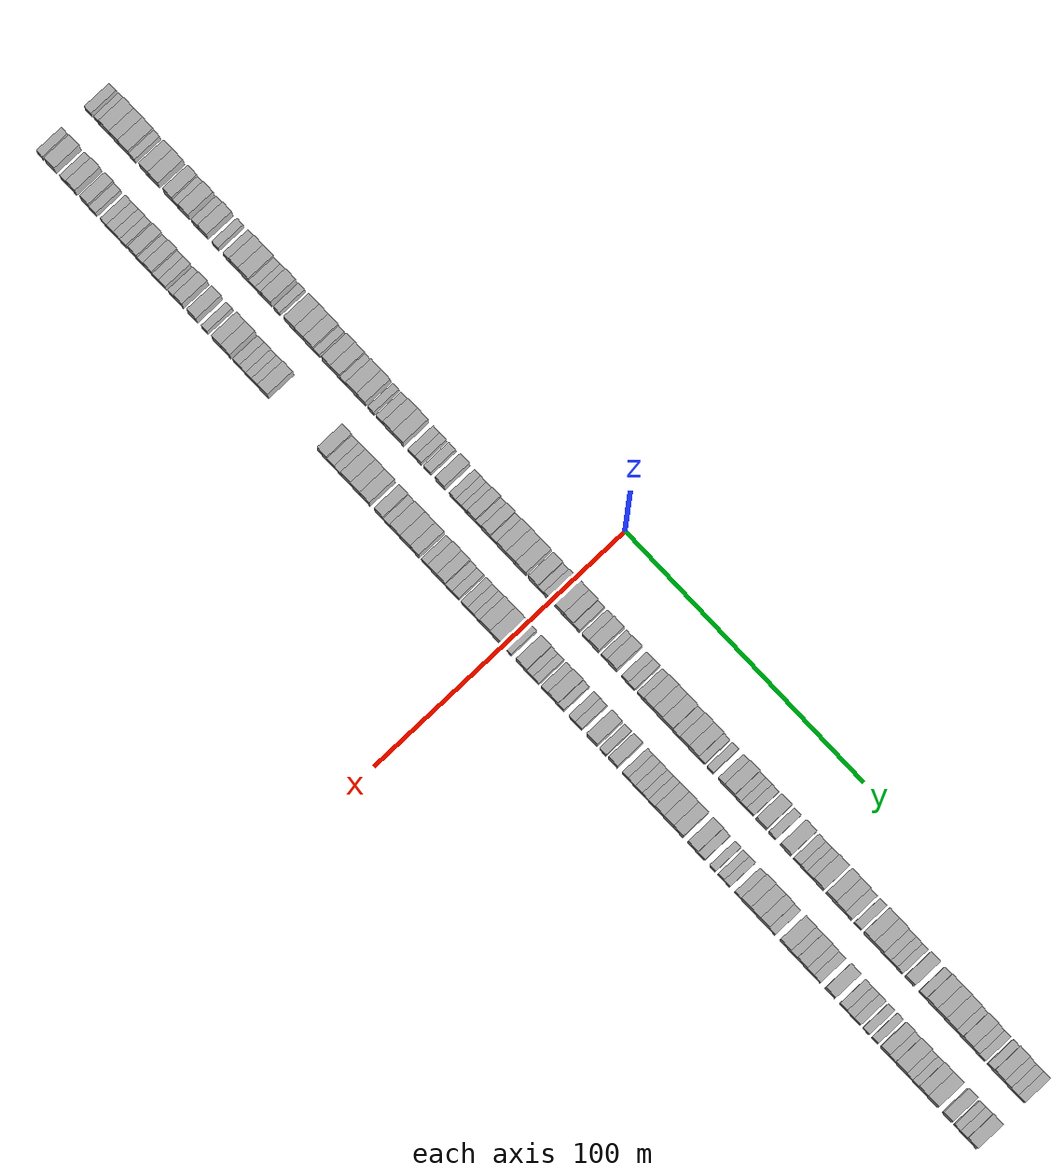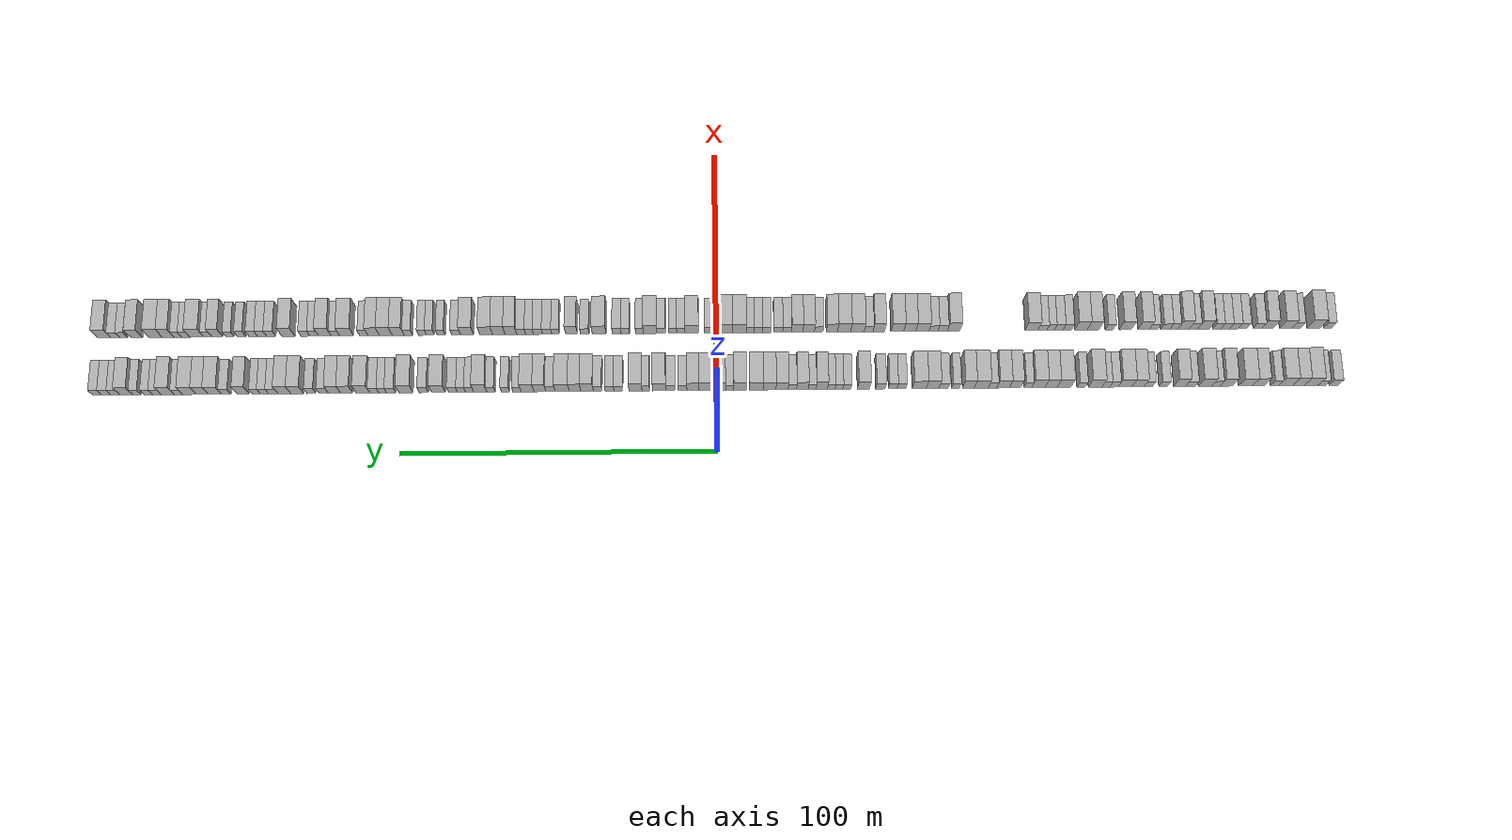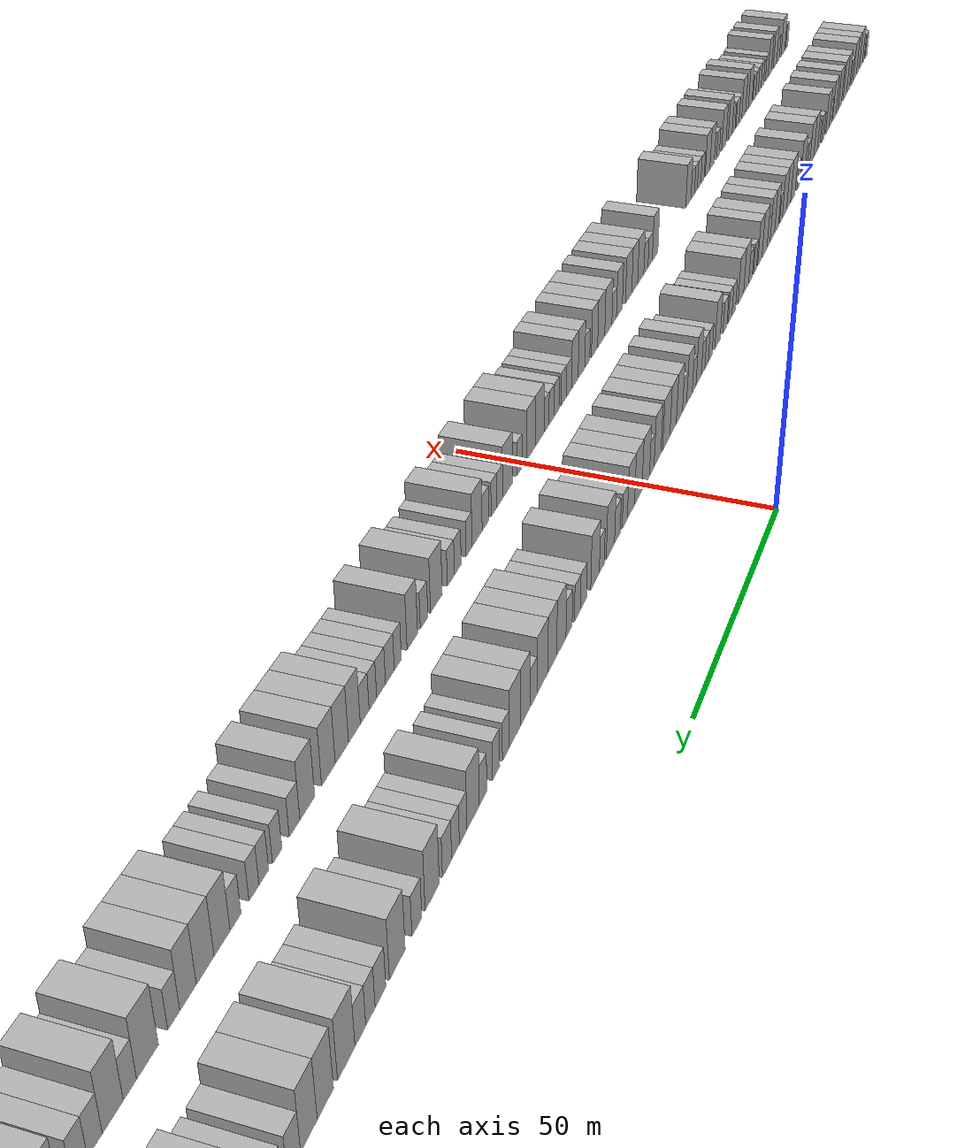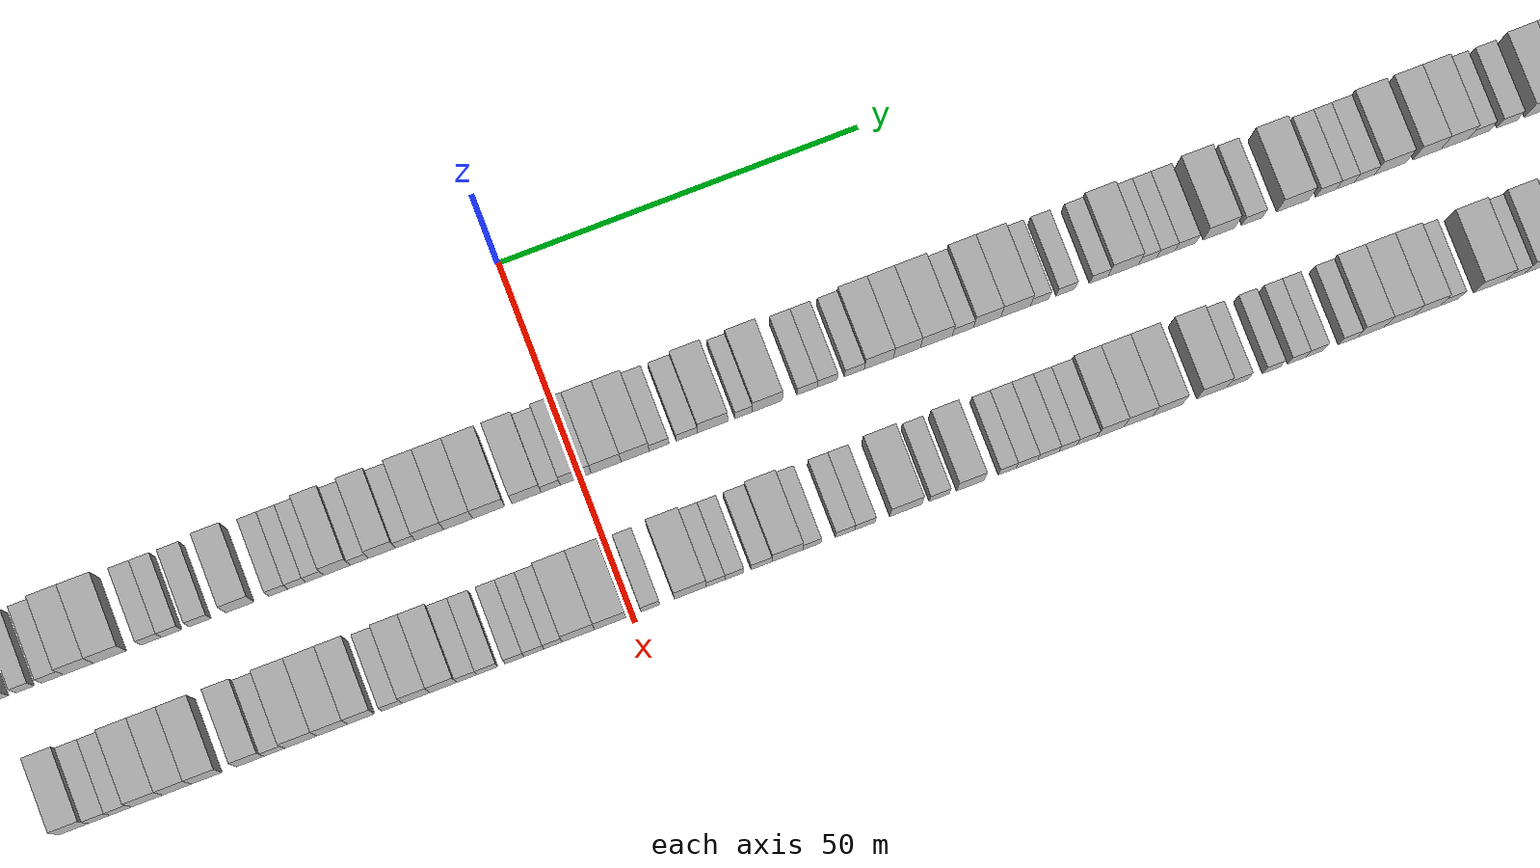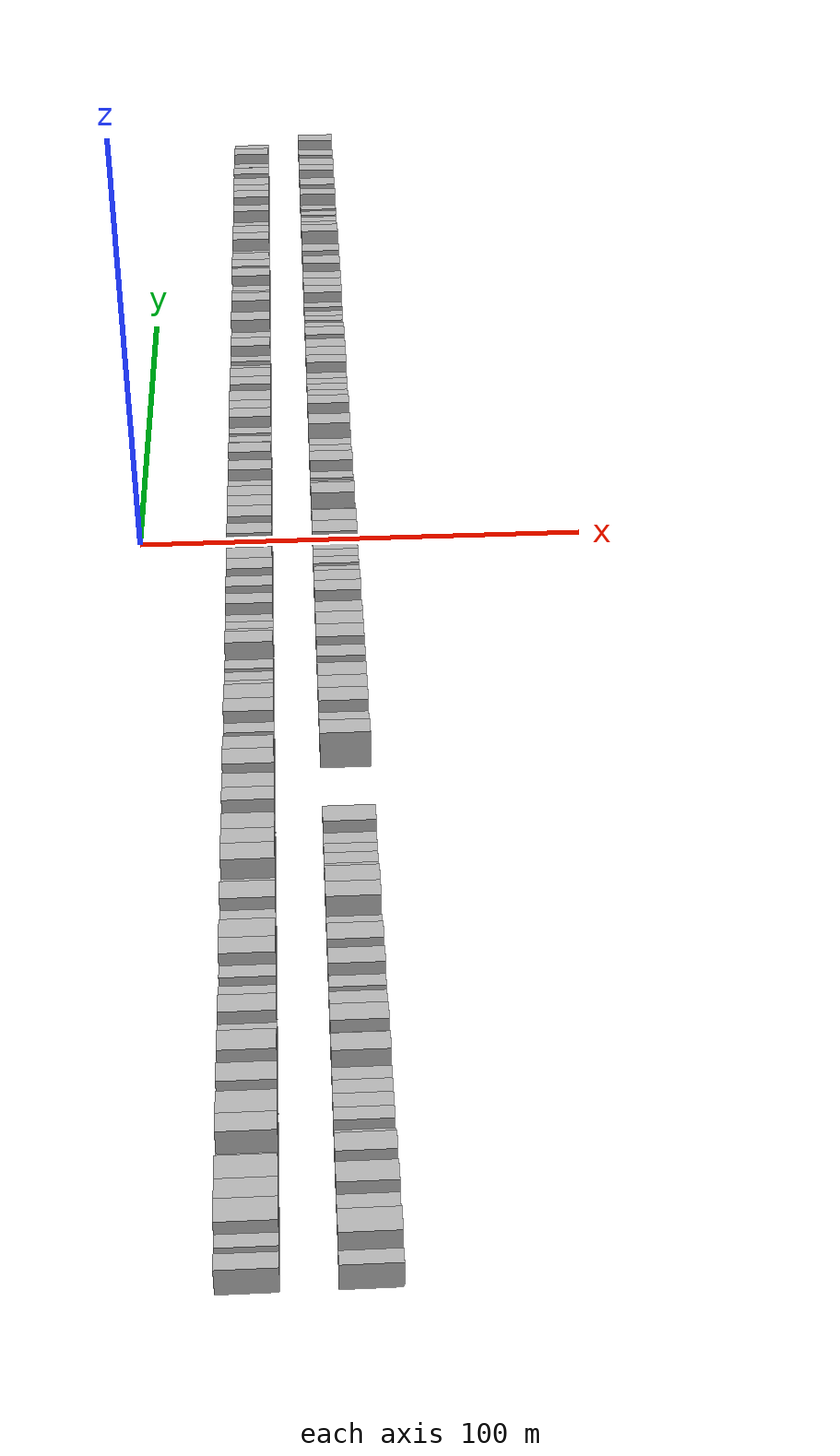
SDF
<sdf version="1.6">
 <world name="default">
  <scene>
   <sky><clouds><speed>12</speed></clouds></sky>
   <ambient>0.4 0.4 0.4 1</ambient>
   <background>0.7 0.7 0.7 1</background>
   <shadows>1</shadows>
  </scene>
  <gravity>0 0 -9.8066</gravity>
  <magnetic_field>6e-06 2.3e-05 -4.2e-05</magnetic_field>
  <physics default="0" name="default_physics" type="ode">
   <ode>
    <solver>
     <type>quick</type>
     <iters>10</iters>
     <sor>1.0</sor>
     <use_dynamic_moi_rescaling>0</use_dynamic_moi_rescaling>
    </solver>
    <constraints>
     <cfm>0</cfm>
     <erp>0.2</erp>
     <contact_max_correcting_vel>100</contact_max_correcting_vel>
     <contact_surface_layer>0.001</contact_surface_layer>
    </constraints>
   </ode>
   <max_step_size>0.004</max_step_size>
   <real_time_factor>1</real_time_factor>
   <real_time_update_rate>250</real_time_update_rate>
  </physics>
  <light name="sun" type="directional">
   <pose>0 0 10 0 0 0</pose>
   <diffuse>0.8 0.8 0.8 1</diffuse>
   <specular>0.2 0.2 0.2 1</specular>
   <attenuation>
    <range>1000</range>
    <constant>0.9</constant>
    <linear>0.01</linear>
    <quadratic>0.001</quadratic>
   </attenuation>
   <direction>-0.5 0.1 -0.9</direction>
  </light>
  <model name="building_1">
   <static>1</static>
   <pose>25.0000 -196.5242 0 0.000000 0.000000 0.000000</pose>
   <link name="link">
    <pose>0 0 3.00 0 0 0</pose>
    <collision name="collision"><geometry><box><size>10.0000 2.9515 6.0000</size></box></geometry></collision>
    <visual name="visual">
     <cast_shadows>0</cast_shadows>
     <geometry><box><size>10.0000 2.9515 6.0000</size></box></geometry>
     <material>
      <script>
       <uri>model://HANNAS_wall/materials/scripts</uri>
       <uri>model://HANNAS_wall/materials/textures</uri>
       <name>vrc/HANNAS_wall</name>
      </script>
     </material>
    </visual>
   </link>
  </model>
  <model name="building_2">
   <static>1</static>
   <pose>25.0000 -192.8124 0 0.000000 0.000000 0.000000</pose>
   <link name="link">
    <pose>0 0 3.00 0 0 0</pose>
    <collision name="collision"><geometry><box><size>10.0000 2.4722 6.0000</size></box></geometry></collision>
    <visual name="visual">
     <cast_shadows>0</cast_shadows>
     <geometry><box><size>10.0000 2.4722 6.0000</size></box></geometry>
     <material>
      <script>
       <uri>model://HANNAS_wall/materials/scripts</uri>
       <uri>model://HANNAS_wall/materials/textures</uri>
       <name>vrc/HANNAS_wall</name>
      </script>
     </material>
    </visual>
   </link>
  </model>
  <model name="building_3">
   <static>1</static>
   <pose>25.0000 -189.3937 0 0.000000 0.000000 0.000000</pose>
   <link name="link">
    <pose>0 0 4.50 0 0 0</pose>
    <collision name="collision"><geometry><box><size>10.0000 4.3651 9.0000</size></box></geometry></collision>
    <visual name="visual">
     <cast_shadows>0</cast_shadows>
     <geometry><box><size>10.0000 4.3651 9.0000</size></box></geometry>
     <material>
      <script>
       <uri>model://HANNAS_wall/materials/scripts</uri>
       <uri>model://HANNAS_wall/materials/textures</uri>
       <name>vrc/HANNAS_wall</name>
      </script>
     </material>
    </visual>
   </link>
  </model>
  <model name="building_4">
   <static>1</static>
   <pose>25.0000 -185.3602 0 0.000000 0.000000 0.000000</pose>
   <link name="link">
    <pose>0 0 4.50 0 0 0</pose>
    <collision name="collision"><geometry><box><size>10.0000 3.7018 9.0000</size></box></geometry></collision>
    <visual name="visual">
     <cast_shadows>0</cast_shadows>
     <geometry><box><size>10.0000 3.7018 9.0000</size></box></geometry>
     <material>
      <script>
       <uri>model://HANNAS_wall/materials/scripts</uri>
       <uri>model://HANNAS_wall/materials/textures</uri>
       <name>vrc/HANNAS_wall</name>
      </script>
     </material>
    </visual>
   </link>
  </model>
  <model name="building_5">
   <static>1</static>
   <pose>25.0000 -181.2810 0 0.000000 0.000000 0.000000</pose>
   <link name="link">
    <pose>0 0 4.50 0 0 0</pose>
    <collision name="collision"><geometry><box><size>10.0000 4.4566 9.0000</size></box></geometry></collision>
    <visual name="visual">
     <cast_shadows>0</cast_shadows>
     <geometry><box><size>10.0000 4.4566 9.0000</size></box></geometry>
     <material>
      <script>
       <uri>model://HANNAS_wall/materials/scripts</uri>
       <uri>model://HANNAS_wall/materials/textures</uri>
       <name>vrc/HANNAS_wall</name>
      </script>
     </material>
    </visual>
   </link>
  </model>
  <model name="building_6">
   <static>1</static>
   <pose>25.0000 -177.7428 0 0.000000 0.000000 0.000000</pose>
   <link name="link">
    <pose>0 0 3.00 0 0 0</pose>
    <collision name="collision"><geometry><box><size>10.0000 2.6198 6.0000</size></box></geometry></collision>
    <visual name="visual">
     <cast_shadows>0</cast_shadows>
     <geometry><box><size>10.0000 2.6198 6.0000</size></box></geometry>
     <material>
      <script>
       <uri>model://HANNAS_wall/materials/scripts</uri>
       <uri>model://HANNAS_wall/materials/textures</uri>
       <name>vrc/HANNAS_wall</name>
      </script>
     </material>
    </visual>
   </link>
  </model>
  <model name="building_7">
   <static>1</static>
   <pose>25.0000 -172.5616 0 0.000000 0.000000 0.000000</pose>
   <link name="link">
    <pose>0 0 4.50 0 0 0</pose>
    <collision name="collision"><geometry><box><size>10.0000 3.7426 9.0000</size></box></geometry></collision>
    <visual name="visual">
     <cast_shadows>0</cast_shadows>
     <geometry><box><size>10.0000 3.7426 9.0000</size></box></geometry>
     <material>
      <script>
       <uri>model://HANNAS_wall/materials/scripts</uri>
       <uri>model://HANNAS_wall/materials/textures</uri>
       <name>vrc/HANNAS_wall</name>
      </script>
     </material>
    </visual>
   </link>
  </model>
  <model name="building_8">
   <static>1</static>
   <pose>25.0000 -168.4594 0 0.000000 0.000000 0.000000</pose>
   <link name="link">
    <pose>0 0 4.50 0 0 0</pose>
    <collision name="collision"><geometry><box><size>10.0000 4.4617 9.0000</size></box></geometry></collision>
    <visual name="visual">
     <cast_shadows>0</cast_shadows>
     <geometry><box><size>10.0000 4.4617 9.0000</size></box></geometry>
     <material>
      <script>
       <uri>model://HANNAS_wall/materials/scripts</uri>
       <uri>model://HANNAS_wall/materials/textures</uri>
       <name>vrc/HANNAS_wall</name>
      </script>
     </material>
    </visual>
   </link>
  </model>
  <model name="building_9">
   <static>1</static>
   <pose>25.0000 -162.2729 0 0.000000 0.000000 0.000000</pose>
   <link name="link">
    <pose>0 0 4.50 0 0 0</pose>
    <collision name="collision"><geometry><box><size>10.0000 3.9113 9.0000</size></box></geometry></collision>
    <visual name="visual">
     <cast_shadows>0</cast_shadows>
     <geometry><box><size>10.0000 3.9113 9.0000</size></box></geometry>
     <material>
      <script>
       <uri>model://HANNAS_wall/materials/scripts</uri>
       <uri>model://HANNAS_wall/materials/textures</uri>
       <name>vrc/HANNAS_wall</name>
      </script>
     </material>
    </visual>
   </link>
  </model>
  <model name="building_10">
   <static>1</static>
   <pose>25.0000 -159.0052 0 0.000000 0.000000 0.000000</pose>
   <link name="link">
    <pose>0 0 3.00 0 0 0</pose>
    <collision name="collision"><geometry><box><size>10.0000 2.6241 6.0000</size></box></geometry></collision>
    <visual name="visual">
     <cast_shadows>0</cast_shadows>
     <geometry><box><size>10.0000 2.6241 6.0000</size></box></geometry>
     <material>
      <script>
       <uri>model://HANNAS_wall/materials/scripts</uri>
       <uri>model://HANNAS_wall/materials/textures</uri>
       <name>vrc/HANNAS_wall</name>
      </script>
     </material>
    </visual>
   </link>
  </model>
  <model name="building_11">
   <static>1</static>
   <pose>25.0000 -155.5330 0 0.000000 0.000000 0.000000</pose>
   <link name="link">
    <pose>0 0 4.50 0 0 0</pose>
    <collision name="collision"><geometry><box><size>10.0000 4.3203 9.0000</size></box></geometry></collision>
    <visual name="visual">
     <cast_shadows>0</cast_shadows>
     <geometry><box><size>10.0000 4.3203 9.0000</size></box></geometry>
     <material>
      <script>
       <uri>model://HANNAS_wall/materials/scripts</uri>
       <uri>model://HANNAS_wall/materials/textures</uri>
       <name>vrc/HANNAS_wall</name>
      </script>
     </material>
    </visual>
   </link>
  </model>
  <model name="building_12">
   <static>1</static>
   <pose>25.0000 -150.8741 0 0.000000 0.000000 0.000000</pose>
   <link name="link">
    <pose>0 0 3.00 0 0 0</pose>
    <collision name="collision"><geometry><box><size>10.0000 2.9976 6.0000</size></box></geometry></collision>
    <visual name="visual">
     <cast_shadows>0</cast_shadows>
     <geometry><box><size>10.0000 2.9976 6.0000</size></box></geometry>
     <material>
      <script>
       <uri>model://HANNAS_wall/materials/scripts</uri>
       <uri>model://HANNAS_wall/materials/textures</uri>
       <name>vrc/HANNAS_wall</name>
      </script>
     </material>
    </visual>
   </link>
  </model>
  <model name="building_13">
   <static>1</static>
   <pose>25.0000 -147.4346 0 0.000000 0.000000 0.000000</pose>
   <link name="link">
    <pose>0 0 4.50 0 0 0</pose>
    <collision name="collision"><geometry><box><size>10.0000 3.8814 9.0000</size></box></geometry></collision>
    <visual name="visual">
     <cast_shadows>0</cast_shadows>
     <geometry><box><size>10.0000 3.8814 9.0000</size></box></geometry>
     <material>
      <script>
       <uri>model://HANNAS_wall/materials/scripts</uri>
       <uri>model://HANNAS_wall/materials/textures</uri>
       <name>vrc/HANNAS_wall</name>
      </script>
     </material>
    </visual>
   </link>
  </model>
  <model name="building_14">
   <static>1</static>
   <pose>25.0000 -142.1445 0 0.000000 0.000000 0.000000</pose>
   <link name="link">
    <pose>0 0 3.00 0 0 0</pose>
    <collision name="collision"><geometry><box><size>10.0000 2.6989 6.0000</size></box></geometry></collision>
    <visual name="visual">
     <cast_shadows>0</cast_shadows>
     <geometry><box><size>10.0000 2.6989 6.0000</size></box></geometry>
     <material>
      <script>
       <uri>model://HANNAS_wall/materials/scripts</uri>
       <uri>model://HANNAS_wall/materials/textures</uri>
       <name>vrc/HANNAS_wall</name>
      </script>
     </material>
    </visual>
   </link>
  </model>
  <model name="building_15">
   <static>1</static>
   <pose>25.0000 -137.3830 0 0.000000 0.000000 0.000000</pose>
   <link name="link">
    <pose>0 0 3.00 0 0 0</pose>
    <collision name="collision"><geometry><box><size>10.0000 2.8241 6.0000</size></box></geometry></collision>
    <visual name="visual">
     <cast_shadows>0</cast_shadows>
     <geometry><box><size>10.0000 2.8241 6.0000</size></box></geometry>
     <material>
      <script>
       <uri>model://HANNAS_wall/materials/scripts</uri>
       <uri>model://HANNAS_wall/materials/textures</uri>
       <name>vrc/HANNAS_wall</name>
      </script>
     </material>
    </visual>
   </link>
  </model>
  <model name="building_16">
   <static>1</static>
   <pose>25.0000 -134.0629 0 0.000000 0.000000 0.000000</pose>
   <link name="link">
    <pose>0 0 4.50 0 0 0</pose>
    <collision name="collision"><geometry><box><size>10.0000 3.8161 9.0000</size></box></geometry></collision>
    <visual name="visual">
     <cast_shadows>0</cast_shadows>
     <geometry><box><size>10.0000 3.8161 9.0000</size></box></geometry>
     <material>
      <script>
       <uri>model://HANNAS_wall/materials/scripts</uri>
       <uri>model://HANNAS_wall/materials/textures</uri>
       <name>vrc/HANNAS_wall</name>
      </script>
     </material>
    </visual>
   </link>
  </model>
  <model name="building_17">
   <static>1</static>
   <pose>25.0000 -129.9621 0 0.000000 0.000000 0.000000</pose>
   <link name="link">
    <pose>0 0 4.50 0 0 0</pose>
    <collision name="collision"><geometry><box><size>10.0000 4.3854 9.0000</size></box></geometry></collision>
    <visual name="visual">
     <cast_shadows>0</cast_shadows>
     <geometry><box><size>10.0000 4.3854 9.0000</size></box></geometry>
     <material>
      <script>
       <uri>model://HANNAS_wall/materials/scripts</uri>
       <uri>model://HANNAS_wall/materials/textures</uri>
       <name>vrc/HANNAS_wall</name>
      </script>
     </material>
    </visual>
   </link>
  </model>
  <model name="building_18">
   <static>1</static>
   <pose>25.0000 -126.4121 0 0.000000 0.000000 0.000000</pose>
   <link name="link">
    <pose>0 0 3.00 0 0 0</pose>
    <collision name="collision"><geometry><box><size>10.0000 2.7147 6.0000</size></box></geometry></collision>
    <visual name="visual">
     <cast_shadows>0</cast_shadows>
     <geometry><box><size>10.0000 2.7147 6.0000</size></box></geometry>
     <material>
      <script>
       <uri>model://HANNAS_wall/materials/scripts</uri>
       <uri>model://HANNAS_wall/materials/textures</uri>
       <name>vrc/HANNAS_wall</name>
      </script>
     </material>
    </visual>
   </link>
  </model>
  <model name="building_19">
   <static>1</static>
   <pose>25.0000 -123.8324 0 0.000000 0.000000 0.000000</pose>
   <link name="link">
    <pose>0 0 3.00 0 0 0</pose>
    <collision name="collision"><geometry><box><size>10.0000 2.4447 6.0000</size></box></geometry></collision>
    <visual name="visual">
     <cast_shadows>0</cast_shadows>
     <geometry><box><size>10.0000 2.4447 6.0000</size></box></geometry>
     <material>
      <script>
       <uri>model://HANNAS_wall/materials/scripts</uri>
       <uri>model://HANNAS_wall/materials/textures</uri>
       <name>vrc/HANNAS_wall</name>
      </script>
     </material>
    </visual>
   </link>
  </model>
  <model name="building_20">
   <static>1</static>
   <pose>25.0000 -120.4541 0 0.000000 0.000000 0.000000</pose>
   <link name="link">
    <pose>0 0 4.50 0 0 0</pose>
    <collision name="collision"><geometry><box><size>10.0000 4.3119 9.0000</size></box></geometry></collision>
    <visual name="visual">
     <cast_shadows>0</cast_shadows>
     <geometry><box><size>10.0000 4.3119 9.0000</size></box></geometry>
     <material>
      <script>
       <uri>model://HANNAS_wall/materials/scripts</uri>
       <uri>model://HANNAS_wall/materials/textures</uri>
       <name>vrc/HANNAS_wall</name>
      </script>
     </material>
    </visual>
   </link>
  </model>
  <model name="building_21">
   <static>1</static>
   <pose>25.0000 -115.9958 0 0.000000 0.000000 0.000000</pose>
   <link name="link">
    <pose>0 0 3.00 0 0 0</pose>
    <collision name="collision"><geometry><box><size>10.0000 2.6047 6.0000</size></box></geometry></collision>
    <visual name="visual">
     <cast_shadows>0</cast_shadows>
     <geometry><box><size>10.0000 2.6047 6.0000</size></box></geometry>
     <material>
      <script>
       <uri>model://HANNAS_wall/materials/scripts</uri>
       <uri>model://HANNAS_wall/materials/textures</uri>
       <name>vrc/HANNAS_wall</name>
      </script>
     </material>
    </visual>
   </link>
  </model>
  <model name="building_22">
   <static>1</static>
   <pose>25.0000 -110.5119 0 0.000000 0.000000 0.000000</pose>
   <link name="link">
    <pose>0 0 4.50 0 0 0</pose>
    <collision name="collision"><geometry><box><size>10.0000 4.3630 9.0000</size></box></geometry></collision>
    <visual name="visual">
     <cast_shadows>0</cast_shadows>
     <geometry><box><size>10.0000 4.3630 9.0000</size></box></geometry>
     <material>
      <script>
       <uri>model://HANNAS_wall/materials/scripts</uri>
       <uri>model://HANNAS_wall/materials/textures</uri>
       <name>vrc/HANNAS_wall</name>
      </script>
     </material>
    </visual>
   </link>
  </model>
  <model name="building_23">
   <static>1</static>
   <pose>25.0000 -106.3995 0 0.000000 0.000000 0.000000</pose>
   <link name="link">
    <pose>0 0 4.50 0 0 0</pose>
    <collision name="collision"><geometry><box><size>10.0000 3.8619 9.0000</size></box></geometry></collision>
    <visual name="visual">
     <cast_shadows>0</cast_shadows>
     <geometry><box><size>10.0000 3.8619 9.0000</size></box></geometry>
     <material>
      <script>
       <uri>model://HANNAS_wall/materials/scripts</uri>
       <uri>model://HANNAS_wall/materials/textures</uri>
       <name>vrc/HANNAS_wall</name>
      </script>
     </material>
    </visual>
   </link>
  </model>
  <model name="building_24">
   <static>1</static>
   <pose>25.0000 -102.3639 0 0.000000 0.000000 0.000000</pose>
   <link name="link">
    <pose>0 0 4.50 0 0 0</pose>
    <collision name="collision"><geometry><box><size>10.0000 4.2093 9.0000</size></box></geometry></collision>
    <visual name="visual">
     <cast_shadows>0</cast_shadows>
     <geometry><box><size>10.0000 4.2093 9.0000</size></box></geometry>
     <material>
      <script>
       <uri>model://HANNAS_wall/materials/scripts</uri>
       <uri>model://HANNAS_wall/materials/textures</uri>
       <name>vrc/HANNAS_wall</name>
      </script>
     </material>
    </visual>
   </link>
  </model>
  <model name="building_25">
   <static>1</static>
   <pose>25.0000 -98.9838 0 0.000000 0.000000 0.000000</pose>
   <link name="link">
    <pose>0 0 3.00 0 0 0</pose>
    <collision name="collision"><geometry><box><size>10.0000 2.5509 6.0000</size></box></geometry></collision>
    <visual name="visual">
     <cast_shadows>0</cast_shadows>
     <geometry><box><size>10.0000 2.5509 6.0000</size></box></geometry>
     <material>
      <script>
       <uri>model://HANNAS_wall/materials/scripts</uri>
       <uri>model://HANNAS_wall/materials/textures</uri>
       <name>vrc/HANNAS_wall</name>
      </script>
     </material>
    </visual>
   </link>
  </model>
  <model name="building_26">
   <static>1</static>
   <pose>25.0000 -94.8883 0 0.000000 0.000000 0.000000</pose>
   <link name="link">
    <pose>0 0 4.50 0 0 0</pose>
    <collision name="collision"><geometry><box><size>10.0000 3.6400 9.0000</size></box></geometry></collision>
    <visual name="visual">
     <cast_shadows>0</cast_shadows>
     <geometry><box><size>10.0000 3.6400 9.0000</size></box></geometry>
     <material>
      <script>
       <uri>model://HANNAS_wall/materials/scripts</uri>
       <uri>model://HANNAS_wall/materials/textures</uri>
       <name>vrc/HANNAS_wall</name>
      </script>
     </material>
    </visual>
   </link>
  </model>
  <model name="building_27">
   <static>1</static>
   <pose>25.0000 -91.0747 0 0.000000 0.000000 0.000000</pose>
   <link name="link">
    <pose>0 0 4.50 0 0 0</pose>
    <collision name="collision"><geometry><box><size>10.0000 3.9872 9.0000</size></box></geometry></collision>
    <visual name="visual">
     <cast_shadows>0</cast_shadows>
     <geometry><box><size>10.0000 3.9872 9.0000</size></box></geometry>
     <material>
      <script>
       <uri>model://HANNAS_wall/materials/scripts</uri>
       <uri>model://HANNAS_wall/materials/textures</uri>
       <name>vrc/HANNAS_wall</name>
      </script>
     </material>
    </visual>
   </link>
  </model>
  <model name="building_28">
   <static>1</static>
   <pose>25.0000 -87.7327 0 0.000000 0.000000 0.000000</pose>
   <link name="link">
    <pose>0 0 3.00 0 0 0</pose>
    <collision name="collision"><geometry><box><size>10.0000 2.6968 6.0000</size></box></geometry></collision>
    <visual name="visual">
     <cast_shadows>0</cast_shadows>
     <geometry><box><size>10.0000 2.6968 6.0000</size></box></geometry>
     <material>
      <script>
       <uri>model://HANNAS_wall/materials/scripts</uri>
       <uri>model://HANNAS_wall/materials/textures</uri>
       <name>vrc/HANNAS_wall</name>
      </script>
     </material>
    </visual>
   </link>
  </model>
  <model name="building_29">
   <static>1</static>
   <pose>25.0000 -84.1509 0 0.000000 0.000000 0.000000</pose>
   <link name="link">
    <pose>0 0 4.50 0 0 0</pose>
    <collision name="collision"><geometry><box><size>10.0000 4.4668 9.0000</size></box></geometry></collision>
    <visual name="visual">
     <cast_shadows>0</cast_shadows>
     <geometry><box><size>10.0000 4.4668 9.0000</size></box></geometry>
     <material>
      <script>
       <uri>model://HANNAS_wall/materials/scripts</uri>
       <uri>model://HANNAS_wall/materials/textures</uri>
       <name>vrc/HANNAS_wall</name>
      </script>
     </material>
    </visual>
   </link>
  </model>
  <model name="building_30">
   <static>1</static>
   <pose>25.0000 -80.0472 0 0.000000 0.000000 0.000000</pose>
   <link name="link">
    <pose>0 0 4.50 0 0 0</pose>
    <collision name="collision"><geometry><box><size>10.0000 3.7407 9.0000</size></box></geometry></collision>
    <visual name="visual">
     <cast_shadows>0</cast_shadows>
     <geometry><box><size>10.0000 3.7407 9.0000</size></box></geometry>
     <material>
      <script>
       <uri>model://HANNAS_wall/materials/scripts</uri>
       <uri>model://HANNAS_wall/materials/textures</uri>
       <name>vrc/HANNAS_wall</name>
      </script>
     </material>
    </visual>
   </link>
  </model>
  <model name="building_31">
   <static>1</static>
   <pose>25.0000 -75.9265 0 0.000000 0.000000 0.000000</pose>
   <link name="link">
    <pose>0 0 3.00 0 0 0</pose>
    <collision name="collision"><geometry><box><size>10.0000 2.5007 6.0000</size></box></geometry></collision>
    <visual name="visual">
     <cast_shadows>0</cast_shadows>
     <geometry><box><size>10.0000 2.5007 6.0000</size></box></geometry>
     <material>
      <script>
       <uri>model://HANNAS_wall/materials/scripts</uri>
       <uri>model://HANNAS_wall/materials/textures</uri>
       <name>vrc/HANNAS_wall</name>
      </script>
     </material>
    </visual>
   </link>
  </model>
  <model name="building_32">
   <static>1</static>
   <pose>25.0000 -72.1785 0 0.000000 0.000000 0.000000</pose>
   <link name="link">
    <pose>0 0 3.00 0 0 0</pose>
    <collision name="collision"><geometry><box><size>10.0000 2.9952 6.0000</size></box></geometry></collision>
    <visual name="visual">
     <cast_shadows>0</cast_shadows>
     <geometry><box><size>10.0000 2.9952 6.0000</size></box></geometry>
     <material>
      <script>
       <uri>model://HANNAS_wall/materials/scripts</uri>
       <uri>model://HANNAS_wall/materials/textures</uri>
       <name>vrc/HANNAS_wall</name>
      </script>
     </material>
    </visual>
   </link>
  </model>
  <model name="building_33">
   <static>1</static>
   <pose>25.0000 -68.6379 0 0.000000 0.000000 0.000000</pose>
   <link name="link">
    <pose>0 0 4.50 0 0 0</pose>
    <collision name="collision"><geometry><box><size>10.0000 4.0860 9.0000</size></box></geometry></collision>
    <visual name="visual">
     <cast_shadows>0</cast_shadows>
     <geometry><box><size>10.0000 4.0860 9.0000</size></box></geometry>
     <material>
      <script>
       <uri>model://HANNAS_wall/materials/scripts</uri>
       <uri>model://HANNAS_wall/materials/textures</uri>
       <name>vrc/HANNAS_wall</name>
      </script>
     </material>
    </visual>
   </link>
  </model>
  <model name="building_34">
   <static>1</static>
   <pose>25.0000 -64.3615 0 0.000000 0.000000 0.000000</pose>
   <link name="link">
    <pose>0 0 4.50 0 0 0</pose>
    <collision name="collision"><geometry><box><size>10.0000 4.4669 9.0000</size></box></geometry></collision>
    <visual name="visual">
     <cast_shadows>0</cast_shadows>
     <geometry><box><size>10.0000 4.4669 9.0000</size></box></geometry>
     <material>
      <script>
       <uri>model://HANNAS_wall/materials/scripts</uri>
       <uri>model://HANNAS_wall/materials/textures</uri>
       <name>vrc/HANNAS_wall</name>
      </script>
     </material>
    </visual>
   </link>
  </model>
  <model name="building_35">
   <static>1</static>
   <pose>25.0000 -58.7191 0 0.000000 0.000000 0.000000</pose>
   <link name="link">
    <pose>0 0 3.00 0 0 0</pose>
    <collision name="collision"><geometry><box><size>10.0000 2.8178 6.0000</size></box></geometry></collision>
    <visual name="visual">
     <cast_shadows>0</cast_shadows>
     <geometry><box><size>10.0000 2.8178 6.0000</size></box></geometry>
     <material>
      <script>
       <uri>model://HANNAS_wall/materials/scripts</uri>
       <uri>model://HANNAS_wall/materials/textures</uri>
       <name>vrc/HANNAS_wall</name>
      </script>
     </material>
    </visual>
   </link>
  </model>
  <model name="building_36">
   <static>1</static>
   <pose>25.0000 -55.9275 0 0.000000 0.000000 0.000000</pose>
   <link name="link">
    <pose>0 0 3.00 0 0 0</pose>
    <collision name="collision"><geometry><box><size>10.0000 2.7654 6.0000</size></box></geometry></collision>
    <visual name="visual">
     <cast_shadows>0</cast_shadows>
     <geometry><box><size>10.0000 2.7654 6.0000</size></box></geometry>
     <material>
      <script>
       <uri>model://HANNAS_wall/materials/scripts</uri>
       <uri>model://HANNAS_wall/materials/textures</uri>
       <name>vrc/HANNAS_wall</name>
      </script>
     </material>
    </visual>
   </link>
  </model>
  <model name="building_37">
   <static>1</static>
   <pose>25.0000 -52.0480 0 0.000000 0.000000 0.000000</pose>
   <link name="link">
    <pose>0 0 3.00 0 0 0</pose>
    <collision name="collision"><geometry><box><size>10.0000 2.9936 6.0000</size></box></geometry></collision>
    <visual name="visual">
     <cast_shadows>0</cast_shadows>
     <geometry><box><size>10.0000 2.9936 6.0000</size></box></geometry>
     <material>
      <script>
       <uri>model://HANNAS_wall/materials/scripts</uri>
       <uri>model://HANNAS_wall/materials/textures</uri>
       <name>vrc/HANNAS_wall</name>
      </script>
     </material>
    </visual>
   </link>
  </model>
  <model name="building_38">
   <static>1</static>
   <pose>25.0000 -46.6086 0 0.000000 0.000000 0.000000</pose>
   <link name="link">
    <pose>0 0 4.50 0 0 0</pose>
    <collision name="collision"><geometry><box><size>10.0000 3.8852 9.0000</size></box></geometry></collision>
    <visual name="visual">
     <cast_shadows>0</cast_shadows>
     <geometry><box><size>10.0000 3.8852 9.0000</size></box></geometry>
     <material>
      <script>
       <uri>model://HANNAS_wall/materials/scripts</uri>
       <uri>model://HANNAS_wall/materials/textures</uri>
       <name>vrc/HANNAS_wall</name>
      </script>
     </material>
    </visual>
   </link>
  </model>
  <model name="building_39">
   <static>1</static>
   <pose>25.0000 -41.3513 0 0.000000 0.000000 0.000000</pose>
   <link name="link">
    <pose>0 0 3.00 0 0 0</pose>
    <collision name="collision"><geometry><box><size>10.0000 2.6293 6.0000</size></box></geometry></collision>
    <visual name="visual">
     <cast_shadows>0</cast_shadows>
     <geometry><box><size>10.0000 2.6293 6.0000</size></box></geometry>
     <material>
      <script>
       <uri>model://HANNAS_wall/materials/scripts</uri>
       <uri>model://HANNAS_wall/materials/textures</uri>
       <name>vrc/HANNAS_wall</name>
      </script>
     </material>
    </visual>
   </link>
  </model>
  <model name="building_40">
   <static>1</static>
   <pose>25.0000 -38.8066 0 0.000000 0.000000 0.000000</pose>
   <link name="link">
    <pose>0 0 3.00 0 0 0</pose>
    <collision name="collision"><geometry><box><size>10.0000 2.4602 6.0000</size></box></geometry></collision>
    <visual name="visual">
     <cast_shadows>0</cast_shadows>
     <geometry><box><size>10.0000 2.4602 6.0000</size></box></geometry>
     <material>
      <script>
       <uri>model://HANNAS_wall/materials/scripts</uri>
       <uri>model://HANNAS_wall/materials/textures</uri>
       <name>vrc/HANNAS_wall</name>
      </script>
     </material>
    </visual>
   </link>
  </model>
  <model name="building_41">
   <static>1</static>
   <pose>25.0000 -36.3595 0 0.000000 0.000000 0.000000</pose>
   <link name="link">
    <pose>0 0 3.00 0 0 0</pose>
    <collision name="collision"><geometry><box><size>10.0000 2.4339 6.0000</size></box></geometry></collision>
    <visual name="visual">
     <cast_shadows>0</cast_shadows>
     <geometry><box><size>10.0000 2.4339 6.0000</size></box></geometry>
     <material>
      <script>
       <uri>model://HANNAS_wall/materials/scripts</uri>
       <uri>model://HANNAS_wall/materials/textures</uri>
       <name>vrc/HANNAS_wall</name>
      </script>
     </material>
    </visual>
   </link>
  </model>
  <model name="building_42">
   <static>1</static>
   <pose>25.0000 -33.3361 0 0.000000 0.000000 0.000000</pose>
   <link name="link">
    <pose>0 0 4.50 0 0 0</pose>
    <collision name="collision"><geometry><box><size>10.0000 3.6129 9.0000</size></box></geometry></collision>
    <visual name="visual">
     <cast_shadows>0</cast_shadows>
     <geometry><box><size>10.0000 3.6129 9.0000</size></box></geometry>
     <material>
      <script>
       <uri>model://HANNAS_wall/materials/scripts</uri>
       <uri>model://HANNAS_wall/materials/textures</uri>
       <name>vrc/HANNAS_wall</name>
      </script>
     </material>
    </visual>
   </link>
  </model>
  <model name="building_43">
   <static>1</static>
   <pose>25.0000 -30.2593 0 0.000000 0.000000 0.000000</pose>
   <link name="link">
    <pose>0 0 3.00 0 0 0</pose>
    <collision name="collision"><geometry><box><size>10.0000 2.5407 6.0000</size></box></geometry></collision>
    <visual name="visual">
     <cast_shadows>0</cast_shadows>
     <geometry><box><size>10.0000 2.5407 6.0000</size></box></geometry>
     <material>
      <script>
       <uri>model://HANNAS_wall/materials/scripts</uri>
       <uri>model://HANNAS_wall/materials/textures</uri>
       <name>vrc/HANNAS_wall</name>
      </script>
     </material>
    </visual>
   </link>
  </model>
  <model name="building_44">
   <static>1</static>
   <pose>25.0000 -27.1466 0 0.000000 0.000000 0.000000</pose>
   <link name="link">
    <pose>0 0 4.50 0 0 0</pose>
    <collision name="collision"><geometry><box><size>10.0000 3.6848 9.0000</size></box></geometry></collision>
    <visual name="visual">
     <cast_shadows>0</cast_shadows>
     <geometry><box><size>10.0000 3.6848 9.0000</size></box></geometry>
     <material>
      <script>
       <uri>model://HANNAS_wall/materials/scripts</uri>
       <uri>model://HANNAS_wall/materials/textures</uri>
       <name>vrc/HANNAS_wall</name>
      </script>
     </material>
    </visual>
   </link>
  </model>
  <model name="building_45">
   <static>1</static>
   <pose>25.0000 -23.9523 0 0.000000 0.000000 0.000000</pose>
   <link name="link">
    <pose>0 0 3.00 0 0 0</pose>
    <collision name="collision"><geometry><box><size>10.0000 2.7040 6.0000</size></box></geometry></collision>
    <visual name="visual">
     <cast_shadows>0</cast_shadows>
     <geometry><box><size>10.0000 2.7040 6.0000</size></box></geometry>
     <material>
      <script>
       <uri>model://HANNAS_wall/materials/scripts</uri>
       <uri>model://HANNAS_wall/materials/textures</uri>
       <name>vrc/HANNAS_wall</name>
      </script>
     </material>
    </visual>
   </link>
  </model>
  <model name="building_46">
   <static>1</static>
   <pose>25.0000 -20.6476 0 0.000000 0.000000 0.000000</pose>
   <link name="link">
    <pose>0 0 4.50 0 0 0</pose>
    <collision name="collision"><geometry><box><size>10.0000 3.9053 9.0000</size></box></geometry></collision>
    <visual name="visual">
     <cast_shadows>0</cast_shadows>
     <geometry><box><size>10.0000 3.9053 9.0000</size></box></geometry>
     <material>
      <script>
       <uri>model://HANNAS_wall/materials/scripts</uri>
       <uri>model://HANNAS_wall/materials/textures</uri>
       <name>vrc/HANNAS_wall</name>
      </script>
     </material>
    </visual>
   </link>
  </model>
  <model name="building_47">
   <static>1</static>
   <pose>25.0000 -16.6951 0 0.000000 0.000000 0.000000</pose>
   <link name="link">
    <pose>0 0 4.50 0 0 0</pose>
    <collision name="collision"><geometry><box><size>10.0000 3.9997 9.0000</size></box></geometry></collision>
    <visual name="visual">
     <cast_shadows>0</cast_shadows>
     <geometry><box><size>10.0000 3.9997 9.0000</size></box></geometry>
     <material>
      <script>
       <uri>model://HANNAS_wall/materials/scripts</uri>
       <uri>model://HANNAS_wall/materials/textures</uri>
       <name>vrc/HANNAS_wall</name>
      </script>
     </material>
    </visual>
   </link>
  </model>
  <model name="building_48">
   <static>1</static>
   <pose>25.0000 -12.4914 0 0.000000 0.000000 0.000000</pose>
   <link name="link">
    <pose>0 0 4.50 0 0 0</pose>
    <collision name="collision"><geometry><box><size>10.0000 4.4078 9.0000</size></box></geometry></collision>
    <visual name="visual">
     <cast_shadows>0</cast_shadows>
     <geometry><box><size>10.0000 4.4078 9.0000</size></box></geometry>
     <material>
      <script>
       <uri>model://HANNAS_wall/materials/scripts</uri>
       <uri>model://HANNAS_wall/materials/textures</uri>
       <name>vrc/HANNAS_wall</name>
      </script>
     </material>
    </visual>
   </link>
  </model>
  <model name="building_49">
   <static>1</static>
   <pose>25.0000 -7.2823 0 0.000000 0.000000 0.000000</pose>
   <link name="link">
    <pose>0 0 4.50 0 0 0</pose>
    <collision name="collision"><geometry><box><size>10.0000 4.0102 9.0000</size></box></geometry></collision>
    <visual name="visual">
     <cast_shadows>0</cast_shadows>
     <geometry><box><size>10.0000 4.0102 9.0000</size></box></geometry>
     <material>
      <script>
       <uri>model://HANNAS_wall/materials/scripts</uri>
       <uri>model://HANNAS_wall/materials/textures</uri>
       <name>vrc/HANNAS_wall</name>
      </script>
     </material>
    </visual>
   </link>
  </model>
  <model name="building_50">
   <static>1</static>
   <pose>25.0000 -3.9681 0 0.000000 0.000000 0.000000</pose>
   <link name="link">
    <pose>0 0 3.00 0 0 0</pose>
    <collision name="collision"><geometry><box><size>10.0000 2.6182 6.0000</size></box></geometry></collision>
    <visual name="visual">
     <cast_shadows>0</cast_shadows>
     <geometry><box><size>10.0000 2.6182 6.0000</size></box></geometry>
     <material>
      <script>
       <uri>model://HANNAS_wall/materials/scripts</uri>
       <uri>model://HANNAS_wall/materials/textures</uri>
       <name>vrc/HANNAS_wall</name>
      </script>
     </material>
    </visual>
   </link>
  </model>
  <model name="building_51">
   <static>1</static>
   <pose>25.0000 -0.5297 0 0.000000 0.000000 0.000000</pose>
   <link name="link">
    <pose>0 0 4.50 0 0 0</pose>
    <collision name="collision"><geometry><box><size>10.0000 4.2588 9.0000</size></box></geometry></collision>
    <visual name="visual">
     <cast_shadows>0</cast_shadows>
     <geometry><box><size>10.0000 4.2588 9.0000</size></box></geometry>
     <material>
      <script>
       <uri>model://HANNAS_wall/materials/scripts</uri>
       <uri>model://HANNAS_wall/materials/textures</uri>
       <name>vrc/HANNAS_wall</name>
      </script>
     </material>
    </visual>
   </link>
  </model>
  <model name="building_52">
   <static>1</static>
   <pose>25.0000 3.6588 0 0.000000 0.000000 0.000000</pose>
   <link name="link">
    <pose>0 0 4.50 0 0 0</pose>
    <collision name="collision"><geometry><box><size>10.0000 4.1181 9.0000</size></box></geometry></collision>
    <visual name="visual">
     <cast_shadows>0</cast_shadows>
     <geometry><box><size>10.0000 4.1181 9.0000</size></box></geometry>
     <material>
      <script>
       <uri>model://HANNAS_wall/materials/scripts</uri>
       <uri>model://HANNAS_wall/materials/textures</uri>
       <name>vrc/HANNAS_wall</name>
      </script>
     </material>
    </visual>
   </link>
  </model>
  <model name="building_53">
   <static>1</static>
   <pose>25.0000 7.6520 0 0.000000 0.000000 0.000000</pose>
   <link name="link">
    <pose>0 0 4.50 0 0 0</pose>
    <collision name="collision"><geometry><box><size>10.0000 3.8685 9.0000</size></box></geometry></collision>
    <visual name="visual">
     <cast_shadows>0</cast_shadows>
     <geometry><box><size>10.0000 3.8685 9.0000</size></box></geometry>
     <material>
      <script>
       <uri>model://HANNAS_wall/materials/scripts</uri>
       <uri>model://HANNAS_wall/materials/textures</uri>
       <name>vrc/HANNAS_wall</name>
      </script>
     </material>
    </visual>
   </link>
  </model>
  <model name="building_54">
   <static>1</static>
   <pose>25.0000 10.9541 0 0.000000 0.000000 0.000000</pose>
   <link name="link">
    <pose>0 0 3.00 0 0 0</pose>
    <collision name="collision"><geometry><box><size>10.0000 2.7357 6.0000</size></box></geometry></collision>
    <visual name="visual">
     <cast_shadows>0</cast_shadows>
     <geometry><box><size>10.0000 2.7357 6.0000</size></box></geometry>
     <material>
      <script>
       <uri>model://HANNAS_wall/materials/scripts</uri>
       <uri>model://HANNAS_wall/materials/textures</uri>
       <name>vrc/HANNAS_wall</name>
      </script>
     </material>
    </visual>
   </link>
  </model>
  <model name="building_55">
   <static>1</static>
   <pose>25.0000 14.8007 0 0.000000 0.000000 0.000000</pose>
   <link name="link">
    <pose>0 0 3.00 0 0 0</pose>
    <collision name="collision"><geometry><box><size>10.0000 2.9574 6.0000</size></box></geometry></collision>
    <visual name="visual">
     <cast_shadows>0</cast_shadows>
     <geometry><box><size>10.0000 2.9574 6.0000</size></box></geometry>
     <material>
      <script>
       <uri>model://HANNAS_wall/materials/scripts</uri>
       <uri>model://HANNAS_wall/materials/textures</uri>
       <name>vrc/HANNAS_wall</name>
      </script>
     </material>
    </visual>
   </link>
  </model>
  <model name="building_56">
   <static>1</static>
   <pose>25.0000 18.3590 0 0.000000 0.000000 0.000000</pose>
   <link name="link">
    <pose>0 0 4.50 0 0 0</pose>
    <collision name="collision"><geometry><box><size>10.0000 4.1594 9.0000</size></box></geometry></collision>
    <visual name="visual">
     <cast_shadows>0</cast_shadows>
     <geometry><box><size>10.0000 4.1594 9.0000</size></box></geometry>
     <material>
      <script>
       <uri>model://HANNAS_wall/materials/scripts</uri>
       <uri>model://HANNAS_wall/materials/textures</uri>
       <name>vrc/HANNAS_wall</name>
      </script>
     </material>
    </visual>
   </link>
  </model>
  <model name="building_57">
   <static>1</static>
   <pose>25.0000 22.6500 0 0.000000 0.000000 0.000000</pose>
   <link name="link">
    <pose>0 0 3.00 0 0 0</pose>
    <collision name="collision"><geometry><box><size>10.0000 2.4225 6.0000</size></box></geometry></collision>
    <visual name="visual">
     <cast_shadows>0</cast_shadows>
     <geometry><box><size>10.0000 2.4225 6.0000</size></box></geometry>
     <material>
      <script>
       <uri>model://HANNAS_wall/materials/scripts</uri>
       <uri>model://HANNAS_wall/materials/textures</uri>
       <name>vrc/HANNAS_wall</name>
      </script>
     </material>
    </visual>
   </link>
  </model>
  <model name="building_58">
   <static>1</static>
   <pose>25.0000 25.9257 0 0.000000 0.000000 0.000000</pose>
   <link name="link">
    <pose>0 0 4.50 0 0 0</pose>
    <collision name="collision"><geometry><box><size>10.0000 4.1289 9.0000</size></box></geometry></collision>
    <visual name="visual">
     <cast_shadows>0</cast_shadows>
     <geometry><box><size>10.0000 4.1289 9.0000</size></box></geometry>
     <material>
      <script>
       <uri>model://HANNAS_wall/materials/scripts</uri>
       <uri>model://HANNAS_wall/materials/textures</uri>
       <name>vrc/HANNAS_wall</name>
      </script>
     </material>
    </visual>
   </link>
  </model>
  <model name="building_59">
   <static>1</static>
   <pose>25.0000 31.4044 0 0.000000 0.000000 0.000000</pose>
   <link name="link">
    <pose>0 0 3.00 0 0 0</pose>
    <collision name="collision"><geometry><box><size>10.0000 2.8285 6.0000</size></box></geometry></collision>
    <visual name="visual">
     <cast_shadows>0</cast_shadows>
     <geometry><box><size>10.0000 2.8285 6.0000</size></box></geometry>
     <material>
      <script>
       <uri>model://HANNAS_wall/materials/scripts</uri>
       <uri>model://HANNAS_wall/materials/textures</uri>
       <name>vrc/HANNAS_wall</name>
      </script>
     </material>
    </visual>
   </link>
  </model>
  <model name="building_60">
   <static>1</static>
   <pose>25.0000 34.1987 0 0.000000 0.000000 0.000000</pose>
   <link name="link">
    <pose>0 0 3.00 0 0 0</pose>
    <collision name="collision"><geometry><box><size>10.0000 2.7600 6.0000</size></box></geometry></collision>
    <visual name="visual">
     <cast_shadows>0</cast_shadows>
     <geometry><box><size>10.0000 2.7600 6.0000</size></box></geometry>
     <material>
      <script>
       <uri>model://HANNAS_wall/materials/scripts</uri>
       <uri>model://HANNAS_wall/materials/textures</uri>
       <name>vrc/HANNAS_wall</name>
      </script>
     </material>
    </visual>
   </link>
  </model>
  <model name="building_61">
   <static>1</static>
   <pose>25.0000 37.9507 0 0.000000 0.000000 0.000000</pose>
   <link name="link">
    <pose>0 0 3.00 0 0 0</pose>
    <collision name="collision"><geometry><box><size>10.0000 2.7439 6.0000</size></box></geometry></collision>
    <visual name="visual">
     <cast_shadows>0</cast_shadows>
     <geometry><box><size>10.0000 2.7439 6.0000</size></box></geometry>
     <material>
      <script>
       <uri>model://HANNAS_wall/materials/scripts</uri>
       <uri>model://HANNAS_wall/materials/textures</uri>
       <name>vrc/HANNAS_wall</name>
      </script>
     </material>
    </visual>
   </link>
  </model>
  <model name="building_62">
   <static>1</static>
   <pose>25.0000 41.3345 0 0.000000 0.000000 0.000000</pose>
   <link name="link">
    <pose>0 0 4.50 0 0 0</pose>
    <collision name="collision"><geometry><box><size>10.0000 4.0237 9.0000</size></box></geometry></collision>
    <visual name="visual">
     <cast_shadows>0</cast_shadows>
     <geometry><box><size>10.0000 4.0237 9.0000</size></box></geometry>
     <material>
      <script>
       <uri>model://HANNAS_wall/materials/scripts</uri>
       <uri>model://HANNAS_wall/materials/textures</uri>
       <name>vrc/HANNAS_wall</name>
      </script>
     </material>
    </visual>
   </link>
  </model>
  <model name="building_63">
   <static>1</static>
   <pose>25.0000 45.2189 0 0.000000 0.000000 0.000000</pose>
   <link name="link">
    <pose>0 0 4.50 0 0 0</pose>
    <collision name="collision"><geometry><box><size>10.0000 3.7451 9.0000</size></box></geometry></collision>
    <visual name="visual">
     <cast_shadows>0</cast_shadows>
     <geometry><box><size>10.0000 3.7451 9.0000</size></box></geometry>
     <material>
      <script>
       <uri>model://HANNAS_wall/materials/scripts</uri>
       <uri>model://HANNAS_wall/materials/textures</uri>
       <name>vrc/HANNAS_wall</name>
      </script>
     </material>
    </visual>
   </link>
  </model>
  <model name="building_64">
   <static>1</static>
   <pose>25.0000 49.3038 0 0.000000 0.000000 0.000000</pose>
   <link name="link">
    <pose>0 0 4.50 0 0 0</pose>
    <collision name="collision"><geometry><box><size>10.0000 4.4248 9.0000</size></box></geometry></collision>
    <visual name="visual">
     <cast_shadows>0</cast_shadows>
     <geometry><box><size>10.0000 4.4248 9.0000</size></box></geometry>
     <material>
      <script>
       <uri>model://HANNAS_wall/materials/scripts</uri>
       <uri>model://HANNAS_wall/materials/textures</uri>
       <name>vrc/HANNAS_wall</name>
      </script>
     </material>
    </visual>
   </link>
  </model>
  <model name="building_65">
   <static>1</static>
   <pose>25.0000 52.9911 0 0.000000 0.000000 0.000000</pose>
   <link name="link">
    <pose>0 0 3.00 0 0 0</pose>
    <collision name="collision"><geometry><box><size>10.0000 2.9499 6.0000</size></box></geometry></collision>
    <visual name="visual">
     <cast_shadows>0</cast_shadows>
     <geometry><box><size>10.0000 2.9499 6.0000</size></box></geometry>
     <material>
      <script>
       <uri>model://HANNAS_wall/materials/scripts</uri>
       <uri>model://HANNAS_wall/materials/textures</uri>
       <name>vrc/HANNAS_wall</name>
      </script>
     </material>
    </visual>
   </link>
  </model>
  <model name="building_66">
   <static>1</static>
   <pose>25.0000 56.3589 0 0.000000 0.000000 0.000000</pose>
   <link name="link">
    <pose>0 0 4.50 0 0 0</pose>
    <collision name="collision"><geometry><box><size>10.0000 3.7856 9.0000</size></box></geometry></collision>
    <visual name="visual">
     <cast_shadows>0</cast_shadows>
     <geometry><box><size>10.0000 3.7856 9.0000</size></box></geometry>
     <material>
      <script>
       <uri>model://HANNAS_wall/materials/scripts</uri>
       <uri>model://HANNAS_wall/materials/textures</uri>
       <name>vrc/HANNAS_wall</name>
      </script>
     </material>
    </visual>
   </link>
  </model>
  <model name="building_67">
   <static>1</static>
   <pose>25.0000 60.3233 0 0.000000 0.000000 0.000000</pose>
   <link name="link">
    <pose>0 0 4.50 0 0 0</pose>
    <collision name="collision"><geometry><box><size>10.0000 4.1433 9.0000</size></box></geometry></collision>
    <visual name="visual">
     <cast_shadows>0</cast_shadows>
     <geometry><box><size>10.0000 4.1433 9.0000</size></box></geometry>
     <material>
      <script>
       <uri>model://HANNAS_wall/materials/scripts</uri>
       <uri>model://HANNAS_wall/materials/textures</uri>
       <name>vrc/HANNAS_wall</name>
      </script>
     </material>
    </visual>
   </link>
  </model>
  <model name="building_68">
   <static>1</static>
   <pose>25.0000 63.6815 0 0.000000 0.000000 0.000000</pose>
   <link name="link">
    <pose>0 0 3.00 0 0 0</pose>
    <collision name="collision"><geometry><box><size>10.0000 2.5730 6.0000</size></box></geometry></collision>
    <visual name="visual">
     <cast_shadows>0</cast_shadows>
     <geometry><box><size>10.0000 2.5730 6.0000</size></box></geometry>
     <material>
      <script>
       <uri>model://HANNAS_wall/materials/scripts</uri>
       <uri>model://HANNAS_wall/materials/textures</uri>
       <name>vrc/HANNAS_wall</name>
      </script>
     </material>
    </visual>
   </link>
  </model>
  <model name="building_69">
   <static>1</static>
   <pose>25.0000 67.2917 0 0.000000 0.000000 0.000000</pose>
   <link name="link">
    <pose>0 0 3.00 0 0 0</pose>
    <collision name="collision"><geometry><box><size>10.0000 2.6474 6.0000</size></box></geometry></collision>
    <visual name="visual">
     <cast_shadows>0</cast_shadows>
     <geometry><box><size>10.0000 2.6474 6.0000</size></box></geometry>
     <material>
      <script>
       <uri>model://HANNAS_wall/materials/scripts</uri>
       <uri>model://HANNAS_wall/materials/textures</uri>
       <name>vrc/HANNAS_wall</name>
      </script>
     </material>
    </visual>
   </link>
  </model>
  <model name="building_70">
   <static>1</static>
   <pose>25.0000 71.9206 0 0.000000 0.000000 0.000000</pose>
   <link name="link">
    <pose>0 0 3.00 0 0 0</pose>
    <collision name="collision"><geometry><box><size>10.0000 2.6103 6.0000</size></box></geometry></collision>
    <visual name="visual">
     <cast_shadows>0</cast_shadows>
     <geometry><box><size>10.0000 2.6103 6.0000</size></box></geometry>
     <material>
      <script>
       <uri>model://HANNAS_wall/materials/scripts</uri>
       <uri>model://HANNAS_wall/materials/textures</uri>
       <name>vrc/HANNAS_wall</name>
      </script>
     </material>
    </visual>
   </link>
  </model>
  <model name="building_71">
   <static>1</static>
   <pose>25.0000 75.3492 0 0.000000 0.000000 0.000000</pose>
   <link name="link">
    <pose>0 0 4.50 0 0 0</pose>
    <collision name="collision"><geometry><box><size>10.0000 4.2471 9.0000</size></box></geometry></collision>
    <visual name="visual">
     <cast_shadows>0</cast_shadows>
     <geometry><box><size>10.0000 4.2471 9.0000</size></box></geometry>
     <material>
      <script>
       <uri>model://HANNAS_wall/materials/scripts</uri>
       <uri>model://HANNAS_wall/materials/textures</uri>
       <name>vrc/HANNAS_wall</name>
      </script>
     </material>
    </visual>
   </link>
  </model>
  <model name="building_72">
   <static>1</static>
   <pose>25.0000 78.7423 0 0.000000 0.000000 0.000000</pose>
   <link name="link">
    <pose>0 0 3.00 0 0 0</pose>
    <collision name="collision"><geometry><box><size>10.0000 2.5389 6.0000</size></box></geometry></collision>
    <visual name="visual">
     <cast_shadows>0</cast_shadows>
     <geometry><box><size>10.0000 2.5389 6.0000</size></box></geometry>
     <material>
      <script>
       <uri>model://HANNAS_wall/materials/scripts</uri>
       <uri>model://HANNAS_wall/materials/textures</uri>
       <name>vrc/HANNAS_wall</name>
      </script>
     </material>
    </visual>
   </link>
  </model>
  <model name="building_73">
   <static>1</static>
   <pose>25.0000 81.2776 0 0.000000 0.000000 0.000000</pose>
   <link name="link">
    <pose>0 0 3.00 0 0 0</pose>
    <collision name="collision"><geometry><box><size>10.0000 2.5317 6.0000</size></box></geometry></collision>
    <visual name="visual">
     <cast_shadows>0</cast_shadows>
     <geometry><box><size>10.0000 2.5317 6.0000</size></box></geometry>
     <material>
      <script>
       <uri>model://HANNAS_wall/materials/scripts</uri>
       <uri>model://HANNAS_wall/materials/textures</uri>
       <name>vrc/HANNAS_wall</name>
      </script>
     </material>
    </visual>
   </link>
  </model>
  <model name="building_74">
   <static>1</static>
   <pose>25.0000 84.0116 0 0.000000 0.000000 0.000000</pose>
   <link name="link">
    <pose>0 0 3.00 0 0 0</pose>
    <collision name="collision"><geometry><box><size>10.0000 2.9365 6.0000</size></box></geometry></collision>
    <visual name="visual">
     <cast_shadows>0</cast_shadows>
     <geometry><box><size>10.0000 2.9365 6.0000</size></box></geometry>
     <material>
      <script>
       <uri>model://HANNAS_wall/materials/scripts</uri>
       <uri>model://HANNAS_wall/materials/textures</uri>
       <name>vrc/HANNAS_wall</name>
      </script>
     </material>
    </visual>
   </link>
  </model>
  <model name="building_75">
   <static>1</static>
   <pose>25.0000 88.6656 0 0.000000 0.000000 0.000000</pose>
   <link name="link">
    <pose>0 0 4.50 0 0 0</pose>
    <collision name="collision"><geometry><box><size>10.0000 4.3715 9.0000</size></box></geometry></collision>
    <visual name="visual">
     <cast_shadows>0</cast_shadows>
     <geometry><box><size>10.0000 4.3715 9.0000</size></box></geometry>
     <material>
      <script>
       <uri>model://HANNAS_wall/materials/scripts</uri>
       <uri>model://HANNAS_wall/materials/textures</uri>
       <name>vrc/HANNAS_wall</name>
      </script>
     </material>
    </visual>
   </link>
  </model>
  <model name="building_76">
   <static>1</static>
   <pose>25.0000 93.3038 0 0.000000 0.000000 0.000000</pose>
   <link name="link">
    <pose>0 0 3.00 0 0 0</pose>
    <collision name="collision"><geometry><box><size>10.0000 2.9049 6.0000</size></box></geometry></collision>
    <visual name="visual">
     <cast_shadows>0</cast_shadows>
     <geometry><box><size>10.0000 2.9049 6.0000</size></box></geometry>
     <material>
      <script>
       <uri>model://HANNAS_wall/materials/scripts</uri>
       <uri>model://HANNAS_wall/materials/textures</uri>
       <name>vrc/HANNAS_wall</name>
      </script>
     </material>
    </visual>
   </link>
  </model>
  <model name="building_77">
   <static>1</static>
   <pose>25.0000 98.9863 0 0.000000 0.000000 0.000000</pose>
   <link name="link">
    <pose>0 0 4.50 0 0 0</pose>
    <collision name="collision"><geometry><box><size>10.0000 4.4600 9.0000</size></box></geometry></collision>
    <visual name="visual">
     <cast_shadows>0</cast_shadows>
     <geometry><box><size>10.0000 4.4600 9.0000</size></box></geometry>
     <material>
      <script>
       <uri>model://HANNAS_wall/materials/scripts</uri>
       <uri>model://HANNAS_wall/materials/textures</uri>
       <name>vrc/HANNAS_wall</name>
      </script>
     </material>
    </visual>
   </link>
  </model>
  <model name="building_78">
   <static>1</static>
   <pose>25.0000 103.6691 0 0.000000 0.000000 0.000000</pose>
   <link name="link">
    <pose>0 0 3.00 0 0 0</pose>
    <collision name="collision"><geometry><box><size>10.0000 2.9058 6.0000</size></box></geometry></collision>
    <visual name="visual">
     <cast_shadows>0</cast_shadows>
     <geometry><box><size>10.0000 2.9058 6.0000</size></box></geometry>
     <material>
      <script>
       <uri>model://HANNAS_wall/materials/scripts</uri>
       <uri>model://HANNAS_wall/materials/textures</uri>
       <name>vrc/HANNAS_wall</name>
      </script>
     </material>
    </visual>
   </link>
  </model>
  <model name="building_79">
   <static>1</static>
   <pose>25.0000 106.3759 0 0.000000 0.000000 0.000000</pose>
   <link name="link">
    <pose>0 0 3.00 0 0 0</pose>
    <collision name="collision"><geometry><box><size>10.0000 2.5078 6.0000</size></box></geometry></collision>
    <visual name="visual">
     <cast_shadows>0</cast_shadows>
     <geometry><box><size>10.0000 2.5078 6.0000</size></box></geometry>
     <material>
      <script>
       <uri>model://HANNAS_wall/materials/scripts</uri>
       <uri>model://HANNAS_wall/materials/textures</uri>
       <name>vrc/HANNAS_wall</name>
      </script>
     </material>
    </visual>
   </link>
  </model>
  <model name="building_80">
   <static>1</static>
   <pose>25.0000 109.0364 0 0.000000 0.000000 0.000000</pose>
   <link name="link">
    <pose>0 0 3.00 0 0 0</pose>
    <collision name="collision"><geometry><box><size>10.0000 2.8132 6.0000</size></box></geometry></collision>
    <visual name="visual">
     <cast_shadows>0</cast_shadows>
     <geometry><box><size>10.0000 2.8132 6.0000</size></box></geometry>
     <material>
      <script>
       <uri>model://HANNAS_wall/materials/scripts</uri>
       <uri>model://HANNAS_wall/materials/textures</uri>
       <name>vrc/HANNAS_wall</name>
      </script>
     </material>
    </visual>
   </link>
  </model>
  <model name="building_81">
   <static>1</static>
   <pose>25.0000 112.6506 0 0.000000 0.000000 0.000000</pose>
   <link name="link">
    <pose>0 0 4.50 0 0 0</pose>
    <collision name="collision"><geometry><box><size>10.0000 4.4153 9.0000</size></box></geometry></collision>
    <visual name="visual">
     <cast_shadows>0</cast_shadows>
     <geometry><box><size>10.0000 4.4153 9.0000</size></box></geometry>
     <material>
      <script>
       <uri>model://HANNAS_wall/materials/scripts</uri>
       <uri>model://HANNAS_wall/materials/textures</uri>
       <name>vrc/HANNAS_wall</name>
      </script>
     </material>
    </visual>
   </link>
  </model>
  <model name="building_82">
   <static>1</static>
   <pose>25.0000 117.8147 0 0.000000 0.000000 0.000000</pose>
   <link name="link">
    <pose>0 0 4.50 0 0 0</pose>
    <collision name="collision"><geometry><box><size>10.0000 3.9129 9.0000</size></box></geometry></collision>
    <visual name="visual">
     <cast_shadows>0</cast_shadows>
     <geometry><box><size>10.0000 3.9129 9.0000</size></box></geometry>
     <material>
      <script>
       <uri>model://HANNAS_wall/materials/scripts</uri>
       <uri>model://HANNAS_wall/materials/textures</uri>
       <name>vrc/HANNAS_wall</name>
      </script>
     </material>
    </visual>
   </link>
  </model>
  <model name="building_83">
   <static>1</static>
   <pose>25.0000 121.7105 0 0.000000 0.000000 0.000000</pose>
   <link name="link">
    <pose>0 0 4.50 0 0 0</pose>
    <collision name="collision"><geometry><box><size>10.0000 3.8787 9.0000</size></box></geometry></collision>
    <visual name="visual">
     <cast_shadows>0</cast_shadows>
     <geometry><box><size>10.0000 3.8787 9.0000</size></box></geometry>
     <material>
      <script>
       <uri>model://HANNAS_wall/materials/scripts</uri>
       <uri>model://HANNAS_wall/materials/textures</uri>
       <name>vrc/HANNAS_wall</name>
      </script>
     </material>
    </visual>
   </link>
  </model>
  <model name="building_84">
   <static>1</static>
   <pose>25.0000 125.1361 0 0.000000 0.000000 0.000000</pose>
   <link name="link">
    <pose>0 0 3.00 0 0 0</pose>
    <collision name="collision"><geometry><box><size>10.0000 2.9725 6.0000</size></box></geometry></collision>
    <visual name="visual">
     <cast_shadows>0</cast_shadows>
     <geometry><box><size>10.0000 2.9725 6.0000</size></box></geometry>
     <material>
      <script>
       <uri>model://HANNAS_wall/materials/scripts</uri>
       <uri>model://HANNAS_wall/materials/textures</uri>
       <name>vrc/HANNAS_wall</name>
      </script>
     </material>
    </visual>
   </link>
  </model>
  <model name="building_85">
   <static>1</static>
   <pose>25.0000 129.0584 0 0.000000 0.000000 0.000000</pose>
   <link name="link">
    <pose>0 0 3.00 0 0 0</pose>
    <collision name="collision"><geometry><box><size>10.0000 2.8722 6.0000</size></box></geometry></collision>
    <visual name="visual">
     <cast_shadows>0</cast_shadows>
     <geometry><box><size>10.0000 2.8722 6.0000</size></box></geometry>
     <material>
      <script>
       <uri>model://HANNAS_wall/materials/scripts</uri>
       <uri>model://HANNAS_wall/materials/textures</uri>
       <name>vrc/HANNAS_wall</name>
      </script>
     </material>
    </visual>
   </link>
  </model>
  <model name="building_86">
   <static>1</static>
   <pose>25.0000 133.5608 0 0.000000 0.000000 0.000000</pose>
   <link name="link">
    <pose>0 0 4.50 0 0 0</pose>
    <collision name="collision"><geometry><box><size>10.0000 4.1327 9.0000</size></box></geometry></collision>
    <visual name="visual">
     <cast_shadows>0</cast_shadows>
     <geometry><box><size>10.0000 4.1327 9.0000</size></box></geometry>
     <material>
      <script>
       <uri>model://HANNAS_wall/materials/scripts</uri>
       <uri>model://HANNAS_wall/materials/textures</uri>
       <name>vrc/HANNAS_wall</name>
      </script>
     </material>
    </visual>
   </link>
  </model>
  <model name="building_87">
   <static>1</static>
   <pose>25.0000 137.6667 0 0.000000 0.000000 0.000000</pose>
   <link name="link">
    <pose>0 0 4.50 0 0 0</pose>
    <collision name="collision"><geometry><box><size>10.0000 4.0789 9.0000</size></box></geometry></collision>
    <visual name="visual">
     <cast_shadows>0</cast_shadows>
     <geometry><box><size>10.0000 4.0789 9.0000</size></box></geometry>
     <material>
      <script>
       <uri>model://HANNAS_wall/materials/scripts</uri>
       <uri>model://HANNAS_wall/materials/textures</uri>
       <name>vrc/HANNAS_wall</name>
      </script>
     </material>
    </visual>
   </link>
  </model>
  <model name="building_88">
   <static>1</static>
   <pose>25.0000 141.2052 0 0.000000 0.000000 0.000000</pose>
   <link name="link">
    <pose>0 0 3.00 0 0 0</pose>
    <collision name="collision"><geometry><box><size>10.0000 2.9981 6.0000</size></box></geometry></collision>
    <visual name="visual">
     <cast_shadows>0</cast_shadows>
     <geometry><box><size>10.0000 2.9981 6.0000</size></box></geometry>
     <material>
      <script>
       <uri>model://HANNAS_wall/materials/scripts</uri>
       <uri>model://HANNAS_wall/materials/textures</uri>
       <name>vrc/HANNAS_wall</name>
      </script>
     </material>
    </visual>
   </link>
  </model>
  <model name="building_89">
   <static>1</static>
   <pose>25.0000 144.0304 0 0.000000 0.000000 0.000000</pose>
   <link name="link">
    <pose>0 0 3.00 0 0 0</pose>
    <collision name="collision"><geometry><box><size>10.0000 2.6524 6.0000</size></box></geometry></collision>
    <visual name="visual">
     <cast_shadows>0</cast_shadows>
     <geometry><box><size>10.0000 2.6524 6.0000</size></box></geometry>
     <material>
      <script>
       <uri>model://HANNAS_wall/materials/scripts</uri>
       <uri>model://HANNAS_wall/materials/textures</uri>
       <name>vrc/HANNAS_wall</name>
      </script>
     </material>
    </visual>
   </link>
  </model>
  <model name="building_90">
   <static>1</static>
   <pose>25.0000 146.5695 0 0.000000 0.000000 0.000000</pose>
   <link name="link">
    <pose>0 0 3.00 0 0 0</pose>
    <collision name="collision"><geometry><box><size>10.0000 2.4257 6.0000</size></box></geometry></collision>
    <visual name="visual">
     <cast_shadows>0</cast_shadows>
     <geometry><box><size>10.0000 2.4257 6.0000</size></box></geometry>
     <material>
      <script>
       <uri>model://HANNAS_wall/materials/scripts</uri>
       <uri>model://HANNAS_wall/materials/textures</uri>
       <name>vrc/HANNAS_wall</name>
      </script>
     </material>
    </visual>
   </link>
  </model>
  <model name="building_91">
   <static>1</static>
   <pose>25.0000 150.7055 0 0.000000 0.000000 0.000000</pose>
   <link name="link">
    <pose>0 0 4.50 0 0 0</pose>
    <collision name="collision"><geometry><box><size>10.0000 3.8464 9.0000</size></box></geometry></collision>
    <visual name="visual">
     <cast_shadows>0</cast_shadows>
     <geometry><box><size>10.0000 3.8464 9.0000</size></box></geometry>
     <material>
      <script>
       <uri>model://HANNAS_wall/materials/scripts</uri>
       <uri>model://HANNAS_wall/materials/textures</uri>
       <name>vrc/HANNAS_wall</name>
      </script>
     </material>
    </visual>
   </link>
  </model>
  <model name="building_92">
   <static>1</static>
   <pose>25.0000 156.0804 0 0.000000 0.000000 0.000000</pose>
   <link name="link">
    <pose>0 0 3.00 0 0 0</pose>
    <collision name="collision"><geometry><box><size>10.0000 2.9036 6.0000</size></box></geometry></collision>
    <visual name="visual">
     <cast_shadows>0</cast_shadows>
     <geometry><box><size>10.0000 2.9036 6.0000</size></box></geometry>
     <material>
      <script>
       <uri>model://HANNAS_wall/materials/scripts</uri>
       <uri>model://HANNAS_wall/materials/textures</uri>
       <name>vrc/HANNAS_wall</name>
      </script>
     </material>
    </visual>
   </link>
  </model>
  <model name="building_93">
   <static>1</static>
   <pose>25.0000 159.6761 0 0.000000 0.000000 0.000000</pose>
   <link name="link">
    <pose>0 0 4.50 0 0 0</pose>
    <collision name="collision"><geometry><box><size>10.0000 4.2876 9.0000</size></box></geometry></collision>
    <visual name="visual">
     <cast_shadows>0</cast_shadows>
     <geometry><box><size>10.0000 4.2876 9.0000</size></box></geometry>
     <material>
      <script>
       <uri>model://HANNAS_wall/materials/scripts</uri>
       <uri>model://HANNAS_wall/materials/textures</uri>
       <name>vrc/HANNAS_wall</name>
      </script>
     </material>
    </visual>
   </link>
  </model>
  <model name="building_94">
   <static>1</static>
   <pose>25.0000 163.7129 0 0.000000 0.000000 0.000000</pose>
   <link name="link">
    <pose>0 0 4.50 0 0 0</pose>
    <collision name="collision"><geometry><box><size>10.0000 3.7861 9.0000</size></box></geometry></collision>
    <visual name="visual">
     <cast_shadows>0</cast_shadows>
     <geometry><box><size>10.0000 3.7861 9.0000</size></box></geometry>
     <material>
      <script>
       <uri>model://HANNAS_wall/materials/scripts</uri>
       <uri>model://HANNAS_wall/materials/textures</uri>
       <name>vrc/HANNAS_wall</name>
      </script>
     </material>
    </visual>
   </link>
  </model>
  <model name="building_95">
   <static>1</static>
   <pose>25.0000 167.7849 0 0.000000 0.000000 0.000000</pose>
   <link name="link">
    <pose>0 0 4.50 0 0 0</pose>
    <collision name="collision"><geometry><box><size>10.0000 4.3579 9.0000</size></box></geometry></collision>
    <visual name="visual">
     <cast_shadows>0</cast_shadows>
     <geometry><box><size>10.0000 4.3579 9.0000</size></box></geometry>
     <material>
      <script>
       <uri>model://HANNAS_wall/materials/scripts</uri>
       <uri>model://HANNAS_wall/materials/textures</uri>
       <name>vrc/HANNAS_wall</name>
      </script>
     </material>
    </visual>
   </link>
  </model>
  <model name="building_96">
   <static>1</static>
   <pose>25.0000 171.3018 0 0.000000 0.000000 0.000000</pose>
   <link name="link">
    <pose>0 0 3.00 0 0 0</pose>
    <collision name="collision"><geometry><box><size>10.0000 2.6759 6.0000</size></box></geometry></collision>
    <visual name="visual">
     <cast_shadows>0</cast_shadows>
     <geometry><box><size>10.0000 2.6759 6.0000</size></box></geometry>
     <material>
      <script>
       <uri>model://HANNAS_wall/materials/scripts</uri>
       <uri>model://HANNAS_wall/materials/textures</uri>
       <name>vrc/HANNAS_wall</name>
      </script>
     </material>
    </visual>
   </link>
  </model>
  <model name="building_97">
   <static>1</static>
   <pose>25.0000 174.7092 0 0.000000 0.000000 0.000000</pose>
   <link name="link">
    <pose>0 0 4.50 0 0 0</pose>
    <collision name="collision"><geometry><box><size>10.0000 4.1390 9.0000</size></box></geometry></collision>
    <visual name="visual">
     <cast_shadows>0</cast_shadows>
     <geometry><box><size>10.0000 4.1390 9.0000</size></box></geometry>
     <material>
      <script>
       <uri>model://HANNAS_wall/materials/scripts</uri>
       <uri>model://HANNAS_wall/materials/textures</uri>
       <name>vrc/HANNAS_wall</name>
      </script>
     </material>
    </visual>
   </link>
  </model>
  <model name="building_98">
   <static>1</static>
   <pose>25.0000 178.1788 0 0.000000 0.000000 0.000000</pose>
   <link name="link">
    <pose>0 0 3.00 0 0 0</pose>
    <collision name="collision"><geometry><box><size>10.0000 2.8002 6.0000</size></box></geometry></collision>
    <visual name="visual">
     <cast_shadows>0</cast_shadows>
     <geometry><box><size>10.0000 2.8002 6.0000</size></box></geometry>
     <material>
      <script>
       <uri>model://HANNAS_wall/materials/scripts</uri>
       <uri>model://HANNAS_wall/materials/textures</uri>
       <name>vrc/HANNAS_wall</name>
      </script>
     </material>
    </visual>
   </link>
  </model>
  <model name="building_99">
   <static>1</static>
   <pose>25.0000 180.8631 0 0.000000 0.000000 0.000000</pose>
   <link name="link">
    <pose>0 0 3.00 0 0 0</pose>
    <collision name="collision"><geometry><box><size>10.0000 2.5684 6.0000</size></box></geometry></collision>
    <visual name="visual">
     <cast_shadows>0</cast_shadows>
     <geometry><box><size>10.0000 2.5684 6.0000</size></box></geometry>
     <material>
      <script>
       <uri>model://HANNAS_wall/materials/scripts</uri>
       <uri>model://HANNAS_wall/materials/textures</uri>
       <name>vrc/HANNAS_wall</name>
      </script>
     </material>
    </visual>
   </link>
  </model>
  <model name="building_100">
   <static>1</static>
   <pose>25.0000 184.4745 0 0.000000 0.000000 0.000000</pose>
   <link name="link">
    <pose>0 0 3.00 0 0 0</pose>
    <collision name="collision"><geometry><box><size>10.0000 2.6544 6.0000</size></box></geometry></collision>
    <visual name="visual">
     <cast_shadows>0</cast_shadows>
     <geometry><box><size>10.0000 2.6544 6.0000</size></box></geometry>
     <material>
      <script>
       <uri>model://HANNAS_wall/materials/scripts</uri>
       <uri>model://HANNAS_wall/materials/textures</uri>
       <name>vrc/HANNAS_wall</name>
      </script>
     </material>
    </visual>
   </link>
  </model>
  <model name="building_101">
   <static>1</static>
   <pose>25.0000 187.8325 0 0.000000 0.000000 0.000000</pose>
   <link name="link">
    <pose>0 0 4.50 0 0 0</pose>
    <collision name="collision"><geometry><box><size>10.0000 4.0618 9.0000</size></box></geometry></collision>
    <visual name="visual">
     <cast_shadows>0</cast_shadows>
     <geometry><box><size>10.0000 4.0618 9.0000</size></box></geometry>
     <material>
      <script>
       <uri>model://HANNAS_wall/materials/scripts</uri>
       <uri>model://HANNAS_wall/materials/textures</uri>
       <name>vrc/HANNAS_wall</name>
      </script>
     </material>
    </visual>
   </link>
  </model>
  <model name="building_102">
   <static>1</static>
   <pose>25.0000 191.3025 0 0.000000 0.000000 0.000000</pose>
   <link name="link">
    <pose>0 0 3.00 0 0 0</pose>
    <collision name="collision"><geometry><box><size>10.0000 2.8781 6.0000</size></box></geometry></collision>
    <visual name="visual">
     <cast_shadows>0</cast_shadows>
     <geometry><box><size>10.0000 2.8781 6.0000</size></box></geometry>
     <material>
      <script>
       <uri>model://HANNAS_wall/materials/scripts</uri>
       <uri>model://HANNAS_wall/materials/textures</uri>
       <name>vrc/HANNAS_wall</name>
      </script>
     </material>
    </visual>
   </link>
  </model>
  <model name="building_103">
   <static>1</static>
   <pose>25.0000 194.2213 0 0.000000 0.000000 0.000000</pose>
   <link name="link">
    <pose>0 0 3.00 0 0 0</pose>
    <collision name="collision"><geometry><box><size>10.0000 2.9597 6.0000</size></box></geometry></collision>
    <visual name="visual">
     <cast_shadows>0</cast_shadows>
     <geometry><box><size>10.0000 2.9597 6.0000</size></box></geometry>
     <material>
      <script>
       <uri>model://HANNAS_wall/materials/scripts</uri>
       <uri>model://HANNAS_wall/materials/textures</uri>
       <name>vrc/HANNAS_wall</name>
      </script>
     </material>
    </visual>
   </link>
  </model>
  <model name="building_104">
   <static>1</static>
   <pose>25.0000 197.1024 0 0.000000 0.000000 0.000000</pose>
   <link name="link">
    <pose>0 0 3.00 0 0 0</pose>
    <collision name="collision"><geometry><box><size>10.0000 2.8024 6.0000</size></box></geometry></collision>
    <visual name="visual">
     <cast_shadows>0</cast_shadows>
     <geometry><box><size>10.0000 2.8024 6.0000</size></box></geometry>
     <material>
      <script>
       <uri>model://HANNAS_wall/materials/scripts</uri>
       <uri>model://HANNAS_wall/materials/textures</uri>
       <name>vrc/HANNAS_wall</name>
      </script>
     </material>
    </visual>
   </link>
  </model>
  <model name="building_105">
   <static>1</static>
   <pose>44.0000 -196.6971 0 0.000000 0.000000 0.000000</pose>
   <link name="link">
    <pose>0 0 3.00 0 0 0</pose>
    <collision name="collision"><geometry><box><size>10.0000 2.6058 6.0000</size></box></geometry></collision>
    <visual name="visual">
     <cast_shadows>0</cast_shadows>
     <geometry><box><size>10.0000 2.6058 6.0000</size></box></geometry>
     <material>
      <script>
       <uri>model://HANNAS_wall/materials/scripts</uri>
       <uri>model://HANNAS_wall/materials/textures</uri>
       <name>vrc/HANNAS_wall</name>
      </script>
     </material>
    </visual>
   </link>
  </model>
  <model name="building_106">
   <static>1</static>
   <pose>44.0000 -192.2103 0 0.000000 0.000000 0.000000</pose>
   <link name="link">
    <pose>0 0 4.50 0 0 0</pose>
    <collision name="collision"><geometry><box><size>10.0000 4.3680 9.0000</size></box></geometry></collision>
    <visual name="visual">
     <cast_shadows>0</cast_shadows>
     <geometry><box><size>10.0000 4.3680 9.0000</size></box></geometry>
     <material>
      <script>
       <uri>model://HANNAS_wall/materials/scripts</uri>
       <uri>model://HANNAS_wall/materials/textures</uri>
       <name>vrc/HANNAS_wall</name>
      </script>
     </material>
    </visual>
   </link>
  </model>
  <model name="building_107">
   <static>1</static>
   <pose>44.0000 -186.5565 0 0.000000 0.000000 0.000000</pose>
   <link name="link">
    <pose>0 0 3.00 0 0 0</pose>
    <collision name="collision"><geometry><box><size>10.0000 2.9395 6.0000</size></box></geometry></collision>
    <visual name="visual">
     <cast_shadows>0</cast_shadows>
     <geometry><box><size>10.0000 2.9395 6.0000</size></box></geometry>
     <material>
      <script>
       <uri>model://HANNAS_wall/materials/scripts</uri>
       <uri>model://HANNAS_wall/materials/textures</uri>
       <name>vrc/HANNAS_wall</name>
      </script>
     </material>
    </visual>
   </link>
  </model>
  <model name="building_108">
   <static>1</static>
   <pose>44.0000 -183.1201 0 0.000000 0.000000 0.000000</pose>
   <link name="link">
    <pose>0 0 4.50 0 0 0</pose>
    <collision name="collision"><geometry><box><size>10.0000 3.9334 9.0000</size></box></geometry></collision>
    <visual name="visual">
     <cast_shadows>0</cast_shadows>
     <geometry><box><size>10.0000 3.9334 9.0000</size></box></geometry>
     <material>
      <script>
       <uri>model://HANNAS_wall/materials/scripts</uri>
       <uri>model://HANNAS_wall/materials/textures</uri>
       <name>vrc/HANNAS_wall</name>
      </script>
     </material>
    </visual>
   </link>
  </model>
  <model name="building_109">
   <static>1</static>
   <pose>44.0000 -177.3439 0 0.000000 0.000000 0.000000</pose>
   <link name="link">
    <pose>0 0 4.50 0 0 0</pose>
    <collision name="collision"><geometry><box><size>10.0000 3.6190 9.0000</size></box></geometry></collision>
    <visual name="visual">
     <cast_shadows>0</cast_shadows>
     <geometry><box><size>10.0000 3.6190 9.0000</size></box></geometry>
     <material>
      <script>
       <uri>model://HANNAS_wall/materials/scripts</uri>
       <uri>model://HANNAS_wall/materials/textures</uri>
       <name>vrc/HANNAS_wall</name>
      </script>
     </material>
    </visual>
   </link>
  </model>
  <model name="building_110">
   <static>1</static>
   <pose>44.0000 -174.0780 0 0.000000 0.000000 0.000000</pose>
   <link name="link">
    <pose>0 0 3.00 0 0 0</pose>
    <collision name="collision"><geometry><box><size>10.0000 2.9128 6.0000</size></box></geometry></collision>
    <visual name="visual">
     <cast_shadows>0</cast_shadows>
     <geometry><box><size>10.0000 2.9128 6.0000</size></box></geometry>
     <material>
      <script>
       <uri>model://HANNAS_wall/materials/scripts</uri>
       <uri>model://HANNAS_wall/materials/textures</uri>
       <name>vrc/HANNAS_wall</name>
      </script>
     </material>
    </visual>
   </link>
  </model>
  <model name="building_111">
   <static>1</static>
   <pose>44.0000 -169.3118 0 0.000000 0.000000 0.000000</pose>
   <link name="link">
    <pose>0 0 3.00 0 0 0</pose>
    <collision name="collision"><geometry><box><size>10.0000 2.6195 6.0000</size></box></geometry></collision>
    <visual name="visual">
     <cast_shadows>0</cast_shadows>
     <geometry><box><size>10.0000 2.6195 6.0000</size></box></geometry>
     <material>
      <script>
       <uri>model://HANNAS_wall/materials/scripts</uri>
       <uri>model://HANNAS_wall/materials/textures</uri>
       <name>vrc/HANNAS_wall</name>
      </script>
     </material>
    </visual>
   </link>
  </model>
  <model name="building_112">
   <static>1</static>
   <pose>44.0000 -166.5690 0 0.000000 0.000000 0.000000</pose>
   <link name="link">
    <pose>0 0 3.00 0 0 0</pose>
    <collision name="collision"><geometry><box><size>10.0000 2.8662 6.0000</size></box></geometry></collision>
    <visual name="visual">
     <cast_shadows>0</cast_shadows>
     <geometry><box><size>10.0000 2.8662 6.0000</size></box></geometry>
     <material>
      <script>
       <uri>model://HANNAS_wall/materials/scripts</uri>
       <uri>model://HANNAS_wall/materials/textures</uri>
       <name>vrc/HANNAS_wall</name>
      </script>
     </material>
    </visual>
   </link>
  </model>
  <model name="building_113">
   <static>1</static>
   <pose>44.0000 -163.7237 0 0.000000 0.000000 0.000000</pose>
   <link name="link">
    <pose>0 0 3.00 0 0 0</pose>
    <collision name="collision"><geometry><box><size>10.0000 2.8244 6.0000</size></box></geometry></collision>
    <visual name="visual">
     <cast_shadows>0</cast_shadows>
     <geometry><box><size>10.0000 2.8244 6.0000</size></box></geometry>
     <material>
      <script>
       <uri>model://HANNAS_wall/materials/scripts</uri>
       <uri>model://HANNAS_wall/materials/textures</uri>
       <name>vrc/HANNAS_wall</name>
      </script>
     </material>
    </visual>
   </link>
  </model>
  <model name="building_114">
   <static>1</static>
   <pose>44.0000 -160.9991 0 0.000000 0.000000 0.000000</pose>
   <link name="link">
    <pose>0 0 3.00 0 0 0</pose>
    <collision name="collision"><geometry><box><size>10.0000 2.6246 6.0000</size></box></geometry></collision>
    <visual name="visual">
     <cast_shadows>0</cast_shadows>
     <geometry><box><size>10.0000 2.6246 6.0000</size></box></geometry>
     <material>
      <script>
       <uri>model://HANNAS_wall/materials/scripts</uri>
       <uri>model://HANNAS_wall/materials/textures</uri>
       <name>vrc/HANNAS_wall</name>
      </script>
     </material>
    </visual>
   </link>
  </model>
  <model name="building_115">
   <static>1</static>
   <pose>44.0000 -156.7954 0 0.000000 0.000000 0.000000</pose>
   <link name="link">
    <pose>0 0 4.50 0 0 0</pose>
    <collision name="collision"><geometry><box><size>10.0000 3.7830 9.0000</size></box></geometry></collision>
    <visual name="visual">
     <cast_shadows>0</cast_shadows>
     <geometry><box><size>10.0000 3.7830 9.0000</size></box></geometry>
     <material>
      <script>
       <uri>model://HANNAS_wall/materials/scripts</uri>
       <uri>model://HANNAS_wall/materials/textures</uri>
       <name>vrc/HANNAS_wall</name>
      </script>
     </material>
    </visual>
   </link>
  </model>
  <model name="building_116">
   <static>1</static>
   <pose>44.0000 -153.5171 0 0.000000 0.000000 0.000000</pose>
   <link name="link">
    <pose>0 0 3.00 0 0 0</pose>
    <collision name="collision"><geometry><box><size>10.0000 2.7736 6.0000</size></box></geometry></collision>
    <visual name="visual">
     <cast_shadows>0</cast_shadows>
     <geometry><box><size>10.0000 2.7736 6.0000</size></box></geometry>
     <material>
      <script>
       <uri>model://HANNAS_wall/materials/scripts</uri>
       <uri>model://HANNAS_wall/materials/textures</uri>
       <name>vrc/HANNAS_wall</name>
      </script>
     </material>
    </visual>
   </link>
  </model>
  <model name="building_117">
   <static>1</static>
   <pose>44.0000 -150.2755 0 0.000000 0.000000 0.000000</pose>
   <link name="link">
    <pose>0 0 4.50 0 0 0</pose>
    <collision name="collision"><geometry><box><size>10.0000 3.7096 9.0000</size></box></geometry></collision>
    <visual name="visual">
     <cast_shadows>0</cast_shadows>
     <geometry><box><size>10.0000 3.7096 9.0000</size></box></geometry>
     <material>
      <script>
       <uri>model://HANNAS_wall/materials/scripts</uri>
       <uri>model://HANNAS_wall/materials/textures</uri>
       <name>vrc/HANNAS_wall</name>
      </script>
     </material>
    </visual>
   </link>
  </model>
  <model name="building_118">
   <static>1</static>
   <pose>44.0000 -147.1418 0 0.000000 0.000000 0.000000</pose>
   <link name="link">
    <pose>0 0 3.00 0 0 0</pose>
    <collision name="collision"><geometry><box><size>10.0000 2.5578 6.0000</size></box></geometry></collision>
    <visual name="visual">
     <cast_shadows>0</cast_shadows>
     <geometry><box><size>10.0000 2.5578 6.0000</size></box></geometry>
     <material>
      <script>
       <uri>model://HANNAS_wall/materials/scripts</uri>
       <uri>model://HANNAS_wall/materials/textures</uri>
       <name>vrc/HANNAS_wall</name>
      </script>
     </material>
    </visual>
   </link>
  </model>
  <model name="building_119">
   <static>1</static>
   <pose>44.0000 -144.3736 0 0.000000 0.000000 0.000000</pose>
   <link name="link">
    <pose>0 0 3.00 0 0 0</pose>
    <collision name="collision"><geometry><box><size>10.0000 2.9785 6.0000</size></box></geometry></collision>
    <visual name="visual">
     <cast_shadows>0</cast_shadows>
     <geometry><box><size>10.0000 2.9785 6.0000</size></box></geometry>
     <material>
      <script>
       <uri>model://HANNAS_wall/materials/scripts</uri>
       <uri>model://HANNAS_wall/materials/textures</uri>
       <name>vrc/HANNAS_wall</name>
      </script>
     </material>
    </visual>
   </link>
  </model>
  <model name="building_120">
   <static>1</static>
   <pose>44.0000 -140.5534 0 0.000000 0.000000 0.000000</pose>
   <link name="link">
    <pose>0 0 3.00 0 0 0</pose>
    <collision name="collision"><geometry><box><size>10.0000 2.6619 6.0000</size></box></geometry></collision>
    <visual name="visual">
     <cast_shadows>0</cast_shadows>
     <geometry><box><size>10.0000 2.6619 6.0000</size></box></geometry>
     <material>
      <script>
       <uri>model://HANNAS_wall/materials/scripts</uri>
       <uri>model://HANNAS_wall/materials/textures</uri>
       <name>vrc/HANNAS_wall</name>
      </script>
     </material>
    </visual>
   </link>
  </model>
  <model name="building_121">
   <static>1</static>
   <pose>44.0000 -137.3662 0 0.000000 0.000000 0.000000</pose>
   <link name="link">
    <pose>0 0 4.50 0 0 0</pose>
    <collision name="collision"><geometry><box><size>10.0000 3.7125 9.0000</size></box></geometry></collision>
    <visual name="visual">
     <cast_shadows>0</cast_shadows>
     <geometry><box><size>10.0000 3.7125 9.0000</size></box></geometry>
     <material>
      <script>
       <uri>model://HANNAS_wall/materials/scripts</uri>
       <uri>model://HANNAS_wall/materials/textures</uri>
       <name>vrc/HANNAS_wall</name>
      </script>
     </material>
    </visual>
   </link>
  </model>
  <model name="building_122">
   <static>1</static>
   <pose>44.0000 -131.5418 0 0.000000 0.000000 0.000000</pose>
   <link name="link">
    <pose>0 0 4.50 0 0 0</pose>
    <collision name="collision"><geometry><box><size>10.0000 3.9363 9.0000</size></box></geometry></collision>
    <visual name="visual">
     <cast_shadows>0</cast_shadows>
     <geometry><box><size>10.0000 3.9363 9.0000</size></box></geometry>
     <material>
      <script>
       <uri>model://HANNAS_wall/materials/scripts</uri>
       <uri>model://HANNAS_wall/materials/textures</uri>
       <name>vrc/HANNAS_wall</name>
      </script>
     </material>
    </visual>
   </link>
  </model>
  <model name="building_123">
   <static>1</static>
   <pose>44.0000 -126.3023 0 0.000000 0.000000 0.000000</pose>
   <link name="link">
    <pose>0 0 3.00 0 0 0</pose>
    <collision name="collision"><geometry><box><size>10.0000 2.5428 6.0000</size></box></geometry></collision>
    <visual name="visual">
     <cast_shadows>0</cast_shadows>
     <geometry><box><size>10.0000 2.5428 6.0000</size></box></geometry>
     <material>
      <script>
       <uri>model://HANNAS_wall/materials/scripts</uri>
       <uri>model://HANNAS_wall/materials/textures</uri>
       <name>vrc/HANNAS_wall</name>
      </script>
     </material>
    </visual>
   </link>
  </model>
  <model name="building_124">
   <static>1</static>
   <pose>44.0000 -121.1284 0 0.000000 0.000000 0.000000</pose>
   <link name="link">
    <pose>0 0 4.50 0 0 0</pose>
    <collision name="collision"><geometry><box><size>10.0000 3.8048 9.0000</size></box></geometry></collision>
    <visual name="visual">
     <cast_shadows>0</cast_shadows>
     <geometry><box><size>10.0000 3.8048 9.0000</size></box></geometry>
     <material>
      <script>
       <uri>model://HANNAS_wall/materials/scripts</uri>
       <uri>model://HANNAS_wall/materials/textures</uri>
       <name>vrc/HANNAS_wall</name>
      </script>
     </material>
    </visual>
   </link>
  </model>
  <model name="building_125">
   <static>1</static>
   <pose>44.0000 -117.2162 0 0.000000 0.000000 0.000000</pose>
   <link name="link">
    <pose>0 0 4.50 0 0 0</pose>
    <collision name="collision"><geometry><box><size>10.0000 4.0195 9.0000</size></box></geometry></collision>
    <visual name="visual">
     <cast_shadows>0</cast_shadows>
     <geometry><box><size>10.0000 4.0195 9.0000</size></box></geometry>
     <material>
      <script>
       <uri>model://HANNAS_wall/materials/scripts</uri>
       <uri>model://HANNAS_wall/materials/textures</uri>
       <name>vrc/HANNAS_wall</name>
      </script>
     </material>
    </visual>
   </link>
  </model>
  <model name="building_126">
   <static>1</static>
   <pose>44.0000 -112.8391 0 0.000000 0.000000 0.000000</pose>
   <link name="link">
    <pose>0 0 3.00 0 0 0</pose>
    <collision name="collision"><geometry><box><size>10.0000 2.7347 6.0000</size></box></geometry></collision>
    <visual name="visual">
     <cast_shadows>0</cast_shadows>
     <geometry><box><size>10.0000 2.7347 6.0000</size></box></geometry>
     <material>
      <script>
       <uri>model://HANNAS_wall/materials/scripts</uri>
       <uri>model://HANNAS_wall/materials/textures</uri>
       <name>vrc/HANNAS_wall</name>
      </script>
     </material>
    </visual>
   </link>
  </model>
  <model name="building_127">
   <static>1</static>
   <pose>44.0000 -110.0573 0 0.000000 0.000000 0.000000</pose>
   <link name="link">
    <pose>0 0 3.00 0 0 0</pose>
    <collision name="collision"><geometry><box><size>10.0000 2.8288 6.0000</size></box></geometry></collision>
    <visual name="visual">
     <cast_shadows>0</cast_shadows>
     <geometry><box><size>10.0000 2.8288 6.0000</size></box></geometry>
     <material>
      <script>
       <uri>model://HANNAS_wall/materials/scripts</uri>
       <uri>model://HANNAS_wall/materials/textures</uri>
       <name>vrc/HANNAS_wall</name>
      </script>
     </material>
    </visual>
   </link>
  </model>
  <model name="building_128">
   <static>1</static>
   <pose>44.0000 -107.4376 0 0.000000 0.000000 0.000000</pose>
   <link name="link">
    <pose>0 0 3.00 0 0 0</pose>
    <collision name="collision"><geometry><box><size>10.0000 2.4107 6.0000</size></box></geometry></collision>
    <visual name="visual">
     <cast_shadows>0</cast_shadows>
     <geometry><box><size>10.0000 2.4107 6.0000</size></box></geometry>
     <material>
      <script>
       <uri>model://HANNAS_wall/materials/scripts</uri>
       <uri>model://HANNAS_wall/materials/textures</uri>
       <name>vrc/HANNAS_wall</name>
      </script>
     </material>
    </visual>
   </link>
  </model>
  <model name="building_129">
   <static>1</static>
   <pose>44.0000 -104.7994 0 0.000000 0.000000 0.000000</pose>
   <link name="link">
    <pose>0 0 3.00 0 0 0</pose>
    <collision name="collision"><geometry><box><size>10.0000 2.8656 6.0000</size></box></geometry></collision>
    <visual name="visual">
     <cast_shadows>0</cast_shadows>
     <geometry><box><size>10.0000 2.8656 6.0000</size></box></geometry>
     <material>
      <script>
       <uri>model://HANNAS_wall/materials/scripts</uri>
       <uri>model://HANNAS_wall/materials/textures</uri>
       <name>vrc/HANNAS_wall</name>
      </script>
     </material>
    </visual>
   </link>
  </model>
  <model name="building_130">
   <static>1</static>
   <pose>44.0000 -101.2841 0 0.000000 0.000000 0.000000</pose>
   <link name="link">
    <pose>0 0 4.50 0 0 0</pose>
    <collision name="collision"><geometry><box><size>10.0000 4.1651 9.0000</size></box></geometry></collision>
    <visual name="visual">
     <cast_shadows>0</cast_shadows>
     <geometry><box><size>10.0000 4.1651 9.0000</size></box></geometry>
     <material>
      <script>
       <uri>model://HANNAS_wall/materials/scripts</uri>
       <uri>model://HANNAS_wall/materials/textures</uri>
       <name>vrc/HANNAS_wall</name>
      </script>
     </material>
    </visual>
   </link>
  </model>
  <model name="building_131">
   <static>1</static>
   <pose>44.0000 -76.2037 0 0.000000 0.000000 0.000000</pose>
   <link name="link">
    <pose>0 0 4.50 0 0 0</pose>
    <collision name="collision"><geometry><box><size>10.0000 3.9986 9.0000</size></box></geometry></collision>
    <visual name="visual">
     <cast_shadows>0</cast_shadows>
     <geometry><box><size>10.0000 3.9986 9.0000</size></box></geometry>
     <material>
      <script>
       <uri>model://HANNAS_wall/materials/scripts</uri>
       <uri>model://HANNAS_wall/materials/textures</uri>
       <name>vrc/HANNAS_wall</name>
      </script>
     </material>
    </visual>
   </link>
  </model>
  <model name="building_132">
   <static>1</static>
   <pose>44.0000 -72.7141 0 0.000000 0.000000 0.000000</pose>
   <link name="link">
    <pose>0 0 3.00 0 0 0</pose>
    <collision name="collision"><geometry><box><size>10.0000 2.9807 6.0000</size></box></geometry></collision>
    <visual name="visual">
     <cast_shadows>0</cast_shadows>
     <geometry><box><size>10.0000 2.9807 6.0000</size></box></geometry>
     <material>
      <script>
       <uri>model://HANNAS_wall/materials/scripts</uri>
       <uri>model://HANNAS_wall/materials/textures</uri>
       <name>vrc/HANNAS_wall</name>
      </script>
     </material>
    </visual>
   </link>
  </model>
  <model name="building_133">
   <static>1</static>
   <pose>44.0000 -69.7472 0 0.000000 0.000000 0.000000</pose>
   <link name="link">
    <pose>0 0 3.00 0 0 0</pose>
    <collision name="collision"><geometry><box><size>10.0000 2.9531 6.0000</size></box></geometry></collision>
    <visual name="visual">
     <cast_shadows>0</cast_shadows>
     <geometry><box><size>10.0000 2.9531 6.0000</size></box></geometry>
     <material>
      <script>
       <uri>model://HANNAS_wall/materials/scripts</uri>
       <uri>model://HANNAS_wall/materials/textures</uri>
       <name>vrc/HANNAS_wall</name>
      </script>
     </material>
    </visual>
   </link>
  </model>
  <model name="building_134">
   <static>1</static>
   <pose>44.0000 -66.1834 0 0.000000 0.000000 0.000000</pose>
   <link name="link">
    <pose>0 0 4.50 0 0 0</pose>
    <collision name="collision"><geometry><box><size>10.0000 4.1745 9.0000</size></box></geometry></collision>
    <visual name="visual">
     <cast_shadows>0</cast_shadows>
     <geometry><box><size>10.0000 4.1745 9.0000</size></box></geometry>
     <material>
      <script>
       <uri>model://HANNAS_wall/materials/scripts</uri>
       <uri>model://HANNAS_wall/materials/textures</uri>
       <name>vrc/HANNAS_wall</name>
      </script>
     </material>
    </visual>
   </link>
  </model>
  <model name="building_135">
   <static>1</static>
   <pose>44.0000 -62.1445 0 0.000000 0.000000 0.000000</pose>
   <link name="link">
    <pose>0 0 4.50 0 0 0</pose>
    <collision name="collision"><geometry><box><size>10.0000 3.9033 9.0000</size></box></geometry></collision>
    <visual name="visual">
     <cast_shadows>0</cast_shadows>
     <geometry><box><size>10.0000 3.9033 9.0000</size></box></geometry>
     <material>
      <script>
       <uri>model://HANNAS_wall/materials/scripts</uri>
       <uri>model://HANNAS_wall/materials/textures</uri>
       <name>vrc/HANNAS_wall</name>
      </script>
     </material>
    </visual>
   </link>
  </model>
  <model name="building_136">
   <static>1</static>
   <pose>44.0000 -58.1118 0 0.000000 0.000000 0.000000</pose>
   <link name="link">
    <pose>0 0 4.50 0 0 0</pose>
    <collision name="collision"><geometry><box><size>10.0000 4.1620 9.0000</size></box></geometry></collision>
    <visual name="visual">
     <cast_shadows>0</cast_shadows>
     <geometry><box><size>10.0000 4.1620 9.0000</size></box></geometry>
     <material>
      <script>
       <uri>model://HANNAS_wall/materials/scripts</uri>
       <uri>model://HANNAS_wall/materials/textures</uri>
       <name>vrc/HANNAS_wall</name>
      </script>
     </material>
    </visual>
   </link>
  </model>
  <model name="building_137">
   <static>1</static>
   <pose>44.0000 -52.1697 0 0.000000 0.000000 0.000000</pose>
   <link name="link">
    <pose>0 0 4.50 0 0 0</pose>
    <collision name="collision"><geometry><box><size>10.0000 3.7222 9.0000</size></box></geometry></collision>
    <visual name="visual">
     <cast_shadows>0</cast_shadows>
     <geometry><box><size>10.0000 3.7222 9.0000</size></box></geometry>
     <material>
      <script>
       <uri>model://HANNAS_wall/materials/scripts</uri>
       <uri>model://HANNAS_wall/materials/textures</uri>
       <name>vrc/HANNAS_wall</name>
      </script>
     </material>
    </visual>
   </link>
  </model>
  <model name="building_138">
   <static>1</static>
   <pose>44.0000 -48.8975 0 0.000000 0.000000 0.000000</pose>
   <link name="link">
    <pose>0 0 3.00 0 0 0</pose>
    <collision name="collision"><geometry><box><size>10.0000 2.8223 6.0000</size></box></geometry></collision>
    <visual name="visual">
     <cast_shadows>0</cast_shadows>
     <geometry><box><size>10.0000 2.8223 6.0000</size></box></geometry>
     <material>
      <script>
       <uri>model://HANNAS_wall/materials/scripts</uri>
       <uri>model://HANNAS_wall/materials/textures</uri>
       <name>vrc/HANNAS_wall</name>
      </script>
     </material>
    </visual>
   </link>
  </model>
  <model name="building_139">
   <static>1</static>
   <pose>44.0000 -45.2960 0 0.000000 0.000000 0.000000</pose>
   <link name="link">
    <pose>0 0 4.50 0 0 0</pose>
    <collision name="collision"><geometry><box><size>10.0000 4.3806 9.0000</size></box></geometry></collision>
    <visual name="visual">
     <cast_shadows>0</cast_shadows>
     <geometry><box><size>10.0000 4.3806 9.0000</size></box></geometry>
     <material>
      <script>
       <uri>model://HANNAS_wall/materials/scripts</uri>
       <uri>model://HANNAS_wall/materials/textures</uri>
       <name>vrc/HANNAS_wall</name>
      </script>
     </material>
    </visual>
   </link>
  </model>
  <model name="building_140">
   <static>1</static>
   <pose>44.0000 -40.9973 0 0.000000 0.000000 0.000000</pose>
   <link name="link">
    <pose>0 0 4.50 0 0 0</pose>
    <collision name="collision"><geometry><box><size>10.0000 4.2167 9.0000</size></box></geometry></collision>
    <visual name="visual">
     <cast_shadows>0</cast_shadows>
     <geometry><box><size>10.0000 4.2167 9.0000</size></box></geometry>
     <material>
      <script>
       <uri>model://HANNAS_wall/materials/scripts</uri>
       <uri>model://HANNAS_wall/materials/textures</uri>
       <name>vrc/HANNAS_wall</name>
      </script>
     </material>
    </visual>
   </link>
  </model>
  <model name="building_141">
   <static>1</static>
   <pose>44.0000 -37.0601 0 0.000000 0.000000 0.000000</pose>
   <link name="link">
    <pose>0 0 4.50 0 0 0</pose>
    <collision name="collision"><geometry><box><size>10.0000 3.6578 9.0000</size></box></geometry></collision>
    <visual name="visual">
     <cast_shadows>0</cast_shadows>
     <geometry><box><size>10.0000 3.6578 9.0000</size></box></geometry>
     <material>
      <script>
       <uri>model://HANNAS_wall/materials/scripts</uri>
       <uri>model://HANNAS_wall/materials/textures</uri>
       <name>vrc/HANNAS_wall</name>
      </script>
     </material>
    </visual>
   </link>
  </model>
  <model name="building_142">
   <static>1</static>
   <pose>44.0000 -32.8400 0 0.000000 0.000000 0.000000</pose>
   <link name="link">
    <pose>0 0 3.00 0 0 0</pose>
    <collision name="collision"><geometry><box><size>10.0000 2.7825 6.0000</size></box></geometry></collision>
    <visual name="visual">
     <cast_shadows>0</cast_shadows>
     <geometry><box><size>10.0000 2.7825 6.0000</size></box></geometry>
     <material>
      <script>
       <uri>model://HANNAS_wall/materials/scripts</uri>
       <uri>model://HANNAS_wall/materials/textures</uri>
       <name>vrc/HANNAS_wall</name>
      </script>
     </material>
    </visual>
   </link>
  </model>
  <model name="building_143">
   <static>1</static>
   <pose>44.0000 -29.5636 0 0.000000 0.000000 0.000000</pose>
   <link name="link">
    <pose>0 0 4.50 0 0 0</pose>
    <collision name="collision"><geometry><box><size>10.0000 3.7702 9.0000</size></box></geometry></collision>
    <visual name="visual">
     <cast_shadows>0</cast_shadows>
     <geometry><box><size>10.0000 3.7702 9.0000</size></box></geometry>
     <material>
      <script>
       <uri>model://HANNAS_wall/materials/scripts</uri>
       <uri>model://HANNAS_wall/materials/textures</uri>
       <name>vrc/HANNAS_wall</name>
      </script>
     </material>
    </visual>
   </link>
  </model>
  <model name="building_144">
   <static>1</static>
   <pose>44.0000 -25.8438 0 0.000000 0.000000 0.000000</pose>
   <link name="link">
    <pose>0 0 4.50 0 0 0</pose>
    <collision name="collision"><geometry><box><size>10.0000 3.6695 9.0000</size></box></geometry></collision>
    <visual name="visual">
     <cast_shadows>0</cast_shadows>
     <geometry><box><size>10.0000 3.6695 9.0000</size></box></geometry>
     <material>
      <script>
       <uri>model://HANNAS_wall/materials/scripts</uri>
       <uri>model://HANNAS_wall/materials/textures</uri>
       <name>vrc/HANNAS_wall</name>
      </script>
     </material>
    </visual>
   </link>
  </model>
  <model name="building_145">
   <static>1</static>
   <pose>44.0000 -22.6212 0 0.000000 0.000000 0.000000</pose>
   <link name="link">
    <pose>0 0 3.00 0 0 0</pose>
    <collision name="collision"><geometry><box><size>10.0000 2.7756 6.0000</size></box></geometry></collision>
    <visual name="visual">
     <cast_shadows>0</cast_shadows>
     <geometry><box><size>10.0000 2.7756 6.0000</size></box></geometry>
     <material>
      <script>
       <uri>model://HANNAS_wall/materials/scripts</uri>
       <uri>model://HANNAS_wall/materials/textures</uri>
       <name>vrc/HANNAS_wall</name>
      </script>
     </material>
    </visual>
   </link>
  </model>
  <model name="building_146">
   <static>1</static>
   <pose>44.0000 -19.8085 0 0.000000 0.000000 0.000000</pose>
   <link name="link">
    <pose>0 0 3.00 0 0 0</pose>
    <collision name="collision"><geometry><box><size>10.0000 2.8499 6.0000</size></box></geometry></collision>
    <visual name="visual">
     <cast_shadows>0</cast_shadows>
     <geometry><box><size>10.0000 2.8499 6.0000</size></box></geometry>
     <material>
      <script>
       <uri>model://HANNAS_wall/materials/scripts</uri>
       <uri>model://HANNAS_wall/materials/textures</uri>
       <name>vrc/HANNAS_wall</name>
      </script>
     </material>
    </visual>
   </link>
  </model>
  <model name="building_147">
   <static>1</static>
   <pose>44.0000 -16.0759 0 0.000000 0.000000 0.000000</pose>
   <link name="link">
    <pose>0 0 3.00 0 0 0</pose>
    <collision name="collision"><geometry><box><size>10.0000 2.6153 6.0000</size></box></geometry></collision>
    <visual name="visual">
     <cast_shadows>0</cast_shadows>
     <geometry><box><size>10.0000 2.6153 6.0000</size></box></geometry>
     <material>
      <script>
       <uri>model://HANNAS_wall/materials/scripts</uri>
       <uri>model://HANNAS_wall/materials/textures</uri>
       <name>vrc/HANNAS_wall</name>
      </script>
     </material>
    </visual>
   </link>
  </model>
  <model name="building_148">
   <static>1</static>
   <pose>44.0000 -13.4187 0 0.000000 0.000000 0.000000</pose>
   <link name="link">
    <pose>0 0 3.00 0 0 0</pose>
    <collision name="collision"><geometry><box><size>10.0000 2.6991 6.0000</size></box></geometry></collision>
    <visual name="visual">
     <cast_shadows>0</cast_shadows>
     <geometry><box><size>10.0000 2.6991 6.0000</size></box></geometry>
     <material>
      <script>
       <uri>model://HANNAS_wall/materials/scripts</uri>
       <uri>model://HANNAS_wall/materials/textures</uri>
       <name>vrc/HANNAS_wall</name>
      </script>
     </material>
    </visual>
   </link>
  </model>
  <model name="building_149">
   <static>1</static>
   <pose>44.0000 -10.8124 0 0.000000 0.000000 0.000000</pose>
   <link name="link">
    <pose>0 0 3.00 0 0 0</pose>
    <collision name="collision"><geometry><box><size>10.0000 2.5134 6.0000</size></box></geometry></collision>
    <visual name="visual">
     <cast_shadows>0</cast_shadows>
     <geometry><box><size>10.0000 2.5134 6.0000</size></box></geometry>
     <material>
      <script>
       <uri>model://HANNAS_wall/materials/scripts</uri>
       <uri>model://HANNAS_wall/materials/textures</uri>
       <name>vrc/HANNAS_wall</name>
      </script>
     </material>
    </visual>
   </link>
  </model>
  <model name="building_150">
   <static>1</static>
   <pose>44.0000 -7.3343 0 0.000000 0.000000 0.000000</pose>
   <link name="link">
    <pose>0 0 4.50 0 0 0</pose>
    <collision name="collision"><geometry><box><size>10.0000 4.4429 9.0000</size></box></geometry></collision>
    <visual name="visual">
     <cast_shadows>0</cast_shadows>
     <geometry><box><size>10.0000 4.4429 9.0000</size></box></geometry>
     <material>
      <script>
       <uri>model://HANNAS_wall/materials/scripts</uri>
       <uri>model://HANNAS_wall/materials/textures</uri>
       <name>vrc/HANNAS_wall</name>
      </script>
     </material>
    </visual>
   </link>
  </model>
  <model name="building_151">
   <static>1</static>
   <pose>44.0000 -2.9360 0 0.000000 0.000000 0.000000</pose>
   <link name="link">
    <pose>0 0 4.50 0 0 0</pose>
    <collision name="collision"><geometry><box><size>10.0000 4.3536 9.0000</size></box></geometry></collision>
    <visual name="visual">
     <cast_shadows>0</cast_shadows>
     <geometry><box><size>10.0000 4.3536 9.0000</size></box></geometry>
     <material>
      <script>
       <uri>model://HANNAS_wall/materials/scripts</uri>
       <uri>model://HANNAS_wall/materials/textures</uri>
       <name>vrc/HANNAS_wall</name>
      </script>
     </material>
    </visual>
   </link>
  </model>
  <model name="building_152">
   <static>1</static>
   <pose>44.0000 2.5306 0 0.000000 0.000000 0.000000</pose>
   <link name="link">
    <pose>0 0 3.00 0 0 0</pose>
    <collision name="collision"><geometry><box><size>10.0000 2.5796 6.0000</size></box></geometry></collision>
    <visual name="visual">
     <cast_shadows>0</cast_shadows>
     <geometry><box><size>10.0000 2.5796 6.0000</size></box></geometry>
     <material>
      <script>
       <uri>model://HANNAS_wall/materials/scripts</uri>
       <uri>model://HANNAS_wall/materials/textures</uri>
       <name>vrc/HANNAS_wall</name>
      </script>
     </material>
    </visual>
   </link>
  </model>
  <model name="building_153">
   <static>1</static>
   <pose>44.0000 8.0228 0 0.000000 0.000000 0.000000</pose>
   <link name="link">
    <pose>0 0 4.50 0 0 0</pose>
    <collision name="collision"><geometry><box><size>10.0000 4.4049 9.0000</size></box></geometry></collision>
    <visual name="visual">
     <cast_shadows>0</cast_shadows>
     <geometry><box><size>10.0000 4.4049 9.0000</size></box></geometry>
     <material>
      <script>
       <uri>model://HANNAS_wall/materials/scripts</uri>
       <uri>model://HANNAS_wall/materials/textures</uri>
       <name>vrc/HANNAS_wall</name>
      </script>
     </material>
    </visual>
   </link>
  </model>
  <model name="building_154">
   <static>1</static>
   <pose>44.0000 11.5204 0 0.000000 0.000000 0.000000</pose>
   <link name="link">
    <pose>0 0 3.00 0 0 0</pose>
    <collision name="collision"><geometry><box><size>10.0000 2.5901 6.0000</size></box></geometry></collision>
    <visual name="visual">
     <cast_shadows>0</cast_shadows>
     <geometry><box><size>10.0000 2.5901 6.0000</size></box></geometry>
     <material>
      <script>
       <uri>model://HANNAS_wall/materials/scripts</uri>
       <uri>model://HANNAS_wall/materials/textures</uri>
       <name>vrc/HANNAS_wall</name>
      </script>
     </material>
    </visual>
   </link>
  </model>
  <model name="building_155">
   <static>1</static>
   <pose>44.0000 14.0881 0 0.000000 0.000000 0.000000</pose>
   <link name="link">
    <pose>0 0 3.00 0 0 0</pose>
    <collision name="collision"><geometry><box><size>10.0000 2.5453 6.0000</size></box></geometry></collision>
    <visual name="visual">
     <cast_shadows>0</cast_shadows>
     <geometry><box><size>10.0000 2.5453 6.0000</size></box></geometry>
     <material>
      <script>
       <uri>model://HANNAS_wall/materials/scripts</uri>
       <uri>model://HANNAS_wall/materials/textures</uri>
       <name>vrc/HANNAS_wall</name>
      </script>
     </material>
    </visual>
   </link>
  </model>
  <model name="building_156">
   <static>1</static>
   <pose>44.0000 17.8029 0 0.000000 0.000000 0.000000</pose>
   <link name="link">
    <pose>0 0 3.00 0 0 0</pose>
    <collision name="collision"><geometry><box><size>10.0000 2.8844 6.0000</size></box></geometry></collision>
    <visual name="visual">
     <cast_shadows>0</cast_shadows>
     <geometry><box><size>10.0000 2.8844 6.0000</size></box></geometry>
     <material>
      <script>
       <uri>model://HANNAS_wall/materials/scripts</uri>
       <uri>model://HANNAS_wall/materials/textures</uri>
       <name>vrc/HANNAS_wall</name>
      </script>
     </material>
    </visual>
   </link>
  </model>
  <model name="building_157">
   <static>1</static>
   <pose>44.0000 21.3688 0 0.000000 0.000000 0.000000</pose>
   <link name="link">
    <pose>0 0 4.50 0 0 0</pose>
    <collision name="collision"><geometry><box><size>10.0000 4.2473 9.0000</size></box></geometry></collision>
    <visual name="visual">
     <cast_shadows>0</cast_shadows>
     <geometry><box><size>10.0000 4.2473 9.0000</size></box></geometry>
     <material>
      <script>
       <uri>model://HANNAS_wall/materials/scripts</uri>
       <uri>model://HANNAS_wall/materials/textures</uri>
       <name>vrc/HANNAS_wall</name>
      </script>
     </material>
    </visual>
   </link>
  </model>
  <model name="building_158">
   <static>1</static>
   <pose>44.0000 24.7327 0 0.000000 0.000000 0.000000</pose>
   <link name="link">
    <pose>0 0 3.00 0 0 0</pose>
    <collision name="collision"><geometry><box><size>10.0000 2.4806 6.0000</size></box></geometry></collision>
    <visual name="visual">
     <cast_shadows>0</cast_shadows>
     <geometry><box><size>10.0000 2.4806 6.0000</size></box></geometry>
     <material>
      <script>
       <uri>model://HANNAS_wall/materials/scripts</uri>
       <uri>model://HANNAS_wall/materials/textures</uri>
       <name>vrc/HANNAS_wall</name>
      </script>
     </material>
    </visual>
   </link>
  </model>
  <model name="building_159">
   <static>1</static>
   <pose>44.0000 29.3204 0 0.000000 0.000000 0.000000</pose>
   <link name="link">
    <pose>0 0 3.00 0 0 0</pose>
    <collision name="collision"><geometry><box><size>10.0000 2.6949 6.0000</size></box></geometry></collision>
    <visual name="visual">
     <cast_shadows>0</cast_shadows>
     <geometry><box><size>10.0000 2.6949 6.0000</size></box></geometry>
     <material>
      <script>
       <uri>model://HANNAS_wall/materials/scripts</uri>
       <uri>model://HANNAS_wall/materials/textures</uri>
       <name>vrc/HANNAS_wall</name>
      </script>
     </material>
    </visual>
   </link>
  </model>
  <model name="building_160">
   <static>1</static>
   <pose>44.0000 32.0682 0 0.000000 0.000000 0.000000</pose>
   <link name="link">
    <pose>0 0 3.00 0 0 0</pose>
    <collision name="collision"><geometry><box><size>10.0000 2.8008 6.0000</size></box></geometry></collision>
    <visual name="visual">
     <cast_shadows>0</cast_shadows>
     <geometry><box><size>10.0000 2.8008 6.0000</size></box></geometry>
     <material>
      <script>
       <uri>model://HANNAS_wall/materials/scripts</uri>
       <uri>model://HANNAS_wall/materials/textures</uri>
       <name>vrc/HANNAS_wall</name>
      </script>
     </material>
    </visual>
   </link>
  </model>
  <model name="building_161">
   <static>1</static>
   <pose>44.0000 37.6922 0 0.000000 0.000000 0.000000</pose>
   <link name="link">
    <pose>0 0 4.50 0 0 0</pose>
    <collision name="collision"><geometry><box><size>10.0000 4.4472 9.0000</size></box></geometry></collision>
    <visual name="visual">
     <cast_shadows>0</cast_shadows>
     <geometry><box><size>10.0000 4.4472 9.0000</size></box></geometry>
     <material>
      <script>
       <uri>model://HANNAS_wall/materials/scripts</uri>
       <uri>model://HANNAS_wall/materials/textures</uri>
       <name>vrc/HANNAS_wall</name>
      </script>
     </material>
    </visual>
   </link>
  </model>
  <model name="building_162">
   <static>1</static>
   <pose>44.0000 42.3064 0 0.000000 0.000000 0.000000</pose>
   <link name="link">
    <pose>0 0 3.00 0 0 0</pose>
    <collision name="collision"><geometry><box><size>10.0000 2.7812 6.0000</size></box></geometry></collision>
    <visual name="visual">
     <cast_shadows>0</cast_shadows>
     <geometry><box><size>10.0000 2.7812 6.0000</size></box></geometry>
     <material>
      <script>
       <uri>model://HANNAS_wall/materials/scripts</uri>
       <uri>model://HANNAS_wall/materials/textures</uri>
       <name>vrc/HANNAS_wall</name>
      </script>
     </material>
    </visual>
   </link>
  </model>
  <model name="building_163">
   <static>1</static>
   <pose>44.0000 46.5816 0 0.000000 0.000000 0.000000</pose>
   <link name="link">
    <pose>0 0 4.50 0 0 0</pose>
    <collision name="collision"><geometry><box><size>10.0000 3.7690 9.0000</size></box></geometry></collision>
    <visual name="visual">
     <cast_shadows>0</cast_shadows>
     <geometry><box><size>10.0000 3.7690 9.0000</size></box></geometry>
     <material>
      <script>
       <uri>model://HANNAS_wall/materials/scripts</uri>
       <uri>model://HANNAS_wall/materials/textures</uri>
       <name>vrc/HANNAS_wall</name>
      </script>
     </material>
    </visual>
   </link>
  </model>
  <model name="building_164">
   <static>1</static>
   <pose>44.0000 51.6932 0 0.000000 0.000000 0.000000</pose>
   <link name="link">
    <pose>0 0 3.00 0 0 0</pose>
    <collision name="collision"><geometry><box><size>10.0000 2.4542 6.0000</size></box></geometry></collision>
    <visual name="visual">
     <cast_shadows>0</cast_shadows>
     <geometry><box><size>10.0000 2.4542 6.0000</size></box></geometry>
     <material>
      <script>
       <uri>model://HANNAS_wall/materials/scripts</uri>
       <uri>model://HANNAS_wall/materials/textures</uri>
       <name>vrc/HANNAS_wall</name>
      </script>
     </material>
    </visual>
   </link>
  </model>
  <model name="building_165">
   <static>1</static>
   <pose>44.0000 54.4148 0 0.000000 0.000000 0.000000</pose>
   <link name="link">
    <pose>0 0 3.00 0 0 0</pose>
    <collision name="collision"><geometry><box><size>10.0000 2.9892 6.0000</size></box></geometry></collision>
    <visual name="visual">
     <cast_shadows>0</cast_shadows>
     <geometry><box><size>10.0000 2.9892 6.0000</size></box></geometry>
     <material>
      <script>
       <uri>model://HANNAS_wall/materials/scripts</uri>
       <uri>model://HANNAS_wall/materials/textures</uri>
       <name>vrc/HANNAS_wall</name>
      </script>
     </material>
    </visual>
   </link>
  </model>
  <model name="building_166">
   <static>1</static>
   <pose>44.0000 57.3825 0 0.000000 0.000000 0.000000</pose>
   <link name="link">
    <pose>0 0 3.00 0 0 0</pose>
    <collision name="collision"><geometry><box><size>10.0000 2.9462 6.0000</size></box></geometry></collision>
    <visual name="visual">
     <cast_shadows>0</cast_shadows>
     <geometry><box><size>10.0000 2.9462 6.0000</size></box></geometry>
     <material>
      <script>
       <uri>model://HANNAS_wall/materials/scripts</uri>
       <uri>model://HANNAS_wall/materials/textures</uri>
       <name>vrc/HANNAS_wall</name>
      </script>
     </material>
    </visual>
   </link>
  </model>
  <model name="building_167">
   <static>1</static>
   <pose>44.0000 60.1119 0 0.000000 0.000000 0.000000</pose>
   <link name="link">
    <pose>0 0 3.00 0 0 0</pose>
    <collision name="collision"><geometry><box><size>10.0000 2.5124 6.0000</size></box></geometry></collision>
    <visual name="visual">
     <cast_shadows>0</cast_shadows>
     <geometry><box><size>10.0000 2.5124 6.0000</size></box></geometry>
     <material>
      <script>
       <uri>model://HANNAS_wall/materials/scripts</uri>
       <uri>model://HANNAS_wall/materials/textures</uri>
       <name>vrc/HANNAS_wall</name>
      </script>
     </material>
    </visual>
   </link>
  </model>
  <model name="building_168">
   <static>1</static>
   <pose>44.0000 62.7855 0 0.000000 0.000000 0.000000</pose>
   <link name="link">
    <pose>0 0 3.00 0 0 0</pose>
    <collision name="collision"><geometry><box><size>10.0000 2.8349 6.0000</size></box></geometry></collision>
    <visual name="visual">
     <cast_shadows>0</cast_shadows>
     <geometry><box><size>10.0000 2.8349 6.0000</size></box></geometry>
     <material>
      <script>
       <uri>model://HANNAS_wall/materials/scripts</uri>
       <uri>model://HANNAS_wall/materials/textures</uri>
       <name>vrc/HANNAS_wall</name>
      </script>
     </material>
    </visual>
   </link>
  </model>
  <model name="building_169">
   <static>1</static>
   <pose>44.0000 66.0563 0 0.000000 0.000000 0.000000</pose>
   <link name="link">
    <pose>0 0 4.50 0 0 0</pose>
    <collision name="collision"><geometry><box><size>10.0000 3.7067 9.0000</size></box></geometry></collision>
    <visual name="visual">
     <cast_shadows>0</cast_shadows>
     <geometry><box><size>10.0000 3.7067 9.0000</size></box></geometry>
     <material>
      <script>
       <uri>model://HANNAS_wall/materials/scripts</uri>
       <uri>model://HANNAS_wall/materials/textures</uri>
       <name>vrc/HANNAS_wall</name>
      </script>
     </material>
    </visual>
   </link>
  </model>
  <model name="building_170">
   <static>1</static>
   <pose>44.0000 69.9287 0 0.000000 0.000000 0.000000</pose>
   <link name="link">
    <pose>0 0 4.50 0 0 0</pose>
    <collision name="collision"><geometry><box><size>10.0000 4.0381 9.0000</size></box></geometry></collision>
    <visual name="visual">
     <cast_shadows>0</cast_shadows>
     <geometry><box><size>10.0000 4.0381 9.0000</size></box></geometry>
     <material>
      <script>
       <uri>model://HANNAS_wall/materials/scripts</uri>
       <uri>model://HANNAS_wall/materials/textures</uri>
       <name>vrc/HANNAS_wall</name>
      </script>
     </material>
    </visual>
   </link>
  </model>
  <model name="building_171">
   <static>1</static>
   <pose>44.0000 73.9835 0 0.000000 0.000000 0.000000</pose>
   <link name="link">
    <pose>0 0 4.50 0 0 0</pose>
    <collision name="collision"><geometry><box><size>10.0000 4.0714 9.0000</size></box></geometry></collision>
    <visual name="visual">
     <cast_shadows>0</cast_shadows>
     <geometry><box><size>10.0000 4.0714 9.0000</size></box></geometry>
     <material>
      <script>
       <uri>model://HANNAS_wall/materials/scripts</uri>
       <uri>model://HANNAS_wall/materials/textures</uri>
       <name>vrc/HANNAS_wall</name>
      </script>
     </material>
    </visual>
   </link>
  </model>
  <model name="building_172">
   <static>1</static>
   <pose>44.0000 80.1145 0 0.000000 0.000000 0.000000</pose>
   <link name="link">
    <pose>0 0 4.50 0 0 0</pose>
    <collision name="collision"><geometry><box><size>10.0000 4.1907 9.0000</size></box></geometry></collision>
    <visual name="visual">
     <cast_shadows>0</cast_shadows>
     <geometry><box><size>10.0000 4.1907 9.0000</size></box></geometry>
     <material>
      <script>
       <uri>model://HANNAS_wall/materials/scripts</uri>
       <uri>model://HANNAS_wall/materials/textures</uri>
       <name>vrc/HANNAS_wall</name>
      </script>
     </material>
    </visual>
   </link>
  </model>
  <model name="building_173">
   <static>1</static>
   <pose>44.0000 83.6709 0 0.000000 0.000000 0.000000</pose>
   <link name="link">
    <pose>0 0 3.00 0 0 0</pose>
    <collision name="collision"><geometry><box><size>10.0000 2.9221 6.0000</size></box></geometry></collision>
    <visual name="visual">
     <cast_shadows>0</cast_shadows>
     <geometry><box><size>10.0000 2.9221 6.0000</size></box></geometry>
     <material>
      <script>
       <uri>model://HANNAS_wall/materials/scripts</uri>
       <uri>model://HANNAS_wall/materials/textures</uri>
       <name>vrc/HANNAS_wall</name>
      </script>
     </material>
    </visual>
   </link>
  </model>
  <model name="building_174">
   <static>1</static>
   <pose>44.0000 88.3877 0 0.000000 0.000000 0.000000</pose>
   <link name="link">
    <pose>0 0 3.00 0 0 0</pose>
    <collision name="collision"><geometry><box><size>10.0000 2.5116 6.0000</size></box></geometry></collision>
    <visual name="visual">
     <cast_shadows>0</cast_shadows>
     <geometry><box><size>10.0000 2.5116 6.0000</size></box></geometry>
     <material>
      <script>
       <uri>model://HANNAS_wall/materials/scripts</uri>
       <uri>model://HANNAS_wall/materials/textures</uri>
       <name>vrc/HANNAS_wall</name>
      </script>
     </material>
    </visual>
   </link>
  </model>
  <model name="building_175">
   <static>1</static>
   <pose>44.0000 91.9021 0 0.000000 0.000000 0.000000</pose>
   <link name="link">
    <pose>0 0 3.00 0 0 0</pose>
    <collision name="collision"><geometry><box><size>10.0000 2.5170 6.0000</size></box></geometry></collision>
    <visual name="visual">
     <cast_shadows>0</cast_shadows>
     <geometry><box><size>10.0000 2.5170 6.0000</size></box></geometry>
     <material>
      <script>
       <uri>model://HANNAS_wall/materials/scripts</uri>
       <uri>model://HANNAS_wall/materials/textures</uri>
       <name>vrc/HANNAS_wall</name>
      </script>
     </material>
    </visual>
   </link>
  </model>
  <model name="building_176">
   <static>1</static>
   <pose>44.0000 94.4269 0 0.000000 0.000000 0.000000</pose>
   <link name="link">
    <pose>0 0 3.00 0 0 0</pose>
    <collision name="collision"><geometry><box><size>10.0000 2.5325 6.0000</size></box></geometry></collision>
    <visual name="visual">
     <cast_shadows>0</cast_shadows>
     <geometry><box><size>10.0000 2.5325 6.0000</size></box></geometry>
     <material>
      <script>
       <uri>model://HANNAS_wall/materials/scripts</uri>
       <uri>model://HANNAS_wall/materials/textures</uri>
       <name>vrc/HANNAS_wall</name>
      </script>
     </material>
    </visual>
   </link>
  </model>
  <model name="building_177">
   <static>1</static>
   <pose>44.0000 99.0194 0 0.000000 0.000000 0.000000</pose>
   <link name="link">
    <pose>0 0 3.00 0 0 0</pose>
    <collision name="collision"><geometry><box><size>10.0000 2.6525 6.0000</size></box></geometry></collision>
    <visual name="visual">
     <cast_shadows>0</cast_shadows>
     <geometry><box><size>10.0000 2.6525 6.0000</size></box></geometry>
     <material>
      <script>
       <uri>model://HANNAS_wall/materials/scripts</uri>
       <uri>model://HANNAS_wall/materials/textures</uri>
       <name>vrc/HANNAS_wall</name>
      </script>
     </material>
    </visual>
   </link>
  </model>
  <model name="building_178">
   <static>1</static>
   <pose>44.0000 102.2600 0 0.000000 0.000000 0.000000</pose>
   <link name="link">
    <pose>0 0 4.50 0 0 0</pose>
    <collision name="collision"><geometry><box><size>10.0000 3.8287 9.0000</size></box></geometry></collision>
    <visual name="visual">
     <cast_shadows>0</cast_shadows>
     <geometry><box><size>10.0000 3.8287 9.0000</size></box></geometry>
     <material>
      <script>
       <uri>model://HANNAS_wall/materials/scripts</uri>
       <uri>model://HANNAS_wall/materials/textures</uri>
       <name>vrc/HANNAS_wall</name>
      </script>
     </material>
    </visual>
   </link>
  </model>
  <model name="building_179">
   <static>1</static>
   <pose>44.0000 106.2275 0 0.000000 0.000000 0.000000</pose>
   <link name="link">
    <pose>0 0 4.50 0 0 0</pose>
    <collision name="collision"><geometry><box><size>10.0000 4.1065 9.0000</size></box></geometry></collision>
    <visual name="visual">
     <cast_shadows>0</cast_shadows>
     <geometry><box><size>10.0000 4.1065 9.0000</size></box></geometry>
     <material>
      <script>
       <uri>model://HANNAS_wall/materials/scripts</uri>
       <uri>model://HANNAS_wall/materials/textures</uri>
       <name>vrc/HANNAS_wall</name>
      </script>
     </material>
    </visual>
   </link>
  </model>
  <model name="building_180">
   <static>1</static>
   <pose>44.0000 110.1261 0 0.000000 0.000000 0.000000</pose>
   <link name="link">
    <pose>0 0 4.50 0 0 0</pose>
    <collision name="collision"><geometry><box><size>10.0000 3.6906 9.0000</size></box></geometry></collision>
    <visual name="visual">
     <cast_shadows>0</cast_shadows>
     <geometry><box><size>10.0000 3.6906 9.0000</size></box></geometry>
     <material>
      <script>
       <uri>model://HANNAS_wall/materials/scripts</uri>
       <uri>model://HANNAS_wall/materials/textures</uri>
       <name>vrc/HANNAS_wall</name>
      </script>
     </material>
    </visual>
   </link>
  </model>
  <model name="building_181">
   <static>1</static>
   <pose>44.0000 113.2884 0 0.000000 0.000000 0.000000</pose>
   <link name="link">
    <pose>0 0 3.00 0 0 0</pose>
    <collision name="collision"><geometry><box><size>10.0000 2.6340 6.0000</size></box></geometry></collision>
    <visual name="visual">
     <cast_shadows>0</cast_shadows>
     <geometry><box><size>10.0000 2.6340 6.0000</size></box></geometry>
     <material>
      <script>
       <uri>model://HANNAS_wall/materials/scripts</uri>
       <uri>model://HANNAS_wall/materials/textures</uri>
       <name>vrc/HANNAS_wall</name>
      </script>
     </material>
    </visual>
   </link>
  </model>
  <model name="building_182">
   <static>1</static>
   <pose>44.0000 118.8533 0 0.000000 0.000000 0.000000</pose>
   <link name="link">
    <pose>0 0 4.50 0 0 0</pose>
    <collision name="collision"><geometry><box><size>10.0000 4.4958 9.0000</size></box></geometry></collision>
    <visual name="visual">
     <cast_shadows>0</cast_shadows>
     <geometry><box><size>10.0000 4.4958 9.0000</size></box></geometry>
     <material>
      <script>
       <uri>model://HANNAS_wall/materials/scripts</uri>
       <uri>model://HANNAS_wall/materials/textures</uri>
       <name>vrc/HANNAS_wall</name>
      </script>
     </material>
    </visual>
   </link>
  </model>
  <model name="building_183">
   <static>1</static>
   <pose>44.0000 122.4400 0 0.000000 0.000000 0.000000</pose>
   <link name="link">
    <pose>0 0 3.00 0 0 0</pose>
    <collision name="collision"><geometry><box><size>10.0000 2.6776 6.0000</size></box></geometry></collision>
    <visual name="visual">
     <cast_shadows>0</cast_shadows>
     <geometry><box><size>10.0000 2.6776 6.0000</size></box></geometry>
     <material>
      <script>
       <uri>model://HANNAS_wall/materials/scripts</uri>
       <uri>model://HANNAS_wall/materials/textures</uri>
       <name>vrc/HANNAS_wall</name>
      </script>
     </material>
    </visual>
   </link>
  </model>
  <model name="building_184">
   <static>1</static>
   <pose>44.0000 125.8126 0 0.000000 0.000000 0.000000</pose>
   <link name="link">
    <pose>0 0 4.50 0 0 0</pose>
    <collision name="collision"><geometry><box><size>10.0000 4.0676 9.0000</size></box></geometry></collision>
    <visual name="visual">
     <cast_shadows>0</cast_shadows>
     <geometry><box><size>10.0000 4.0676 9.0000</size></box></geometry>
     <material>
      <script>
       <uri>model://HANNAS_wall/materials/scripts</uri>
       <uri>model://HANNAS_wall/materials/textures</uri>
       <name>vrc/HANNAS_wall</name>
      </script>
     </material>
    </visual>
   </link>
  </model>
  <model name="building_185">
   <static>1</static>
   <pose>44.0000 129.2490 0 0.000000 0.000000 0.000000</pose>
   <link name="link">
    <pose>0 0 3.00 0 0 0</pose>
    <collision name="collision"><geometry><box><size>10.0000 2.8053 6.0000</size></box></geometry></collision>
    <visual name="visual">
     <cast_shadows>0</cast_shadows>
     <geometry><box><size>10.0000 2.8053 6.0000</size></box></geometry>
     <material>
      <script>
       <uri>model://HANNAS_wall/materials/scripts</uri>
       <uri>model://HANNAS_wall/materials/textures</uri>
       <name>vrc/HANNAS_wall</name>
      </script>
     </material>
    </visual>
   </link>
  </model>
  <model name="building_186">
   <static>1</static>
   <pose>44.0000 132.0639 0 0.000000 0.000000 0.000000</pose>
   <link name="link">
    <pose>0 0 3.00 0 0 0</pose>
    <collision name="collision"><geometry><box><size>10.0000 2.8245 6.0000</size></box></geometry></collision>
    <visual name="visual">
     <cast_shadows>0</cast_shadows>
     <geometry><box><size>10.0000 2.8245 6.0000</size></box></geometry>
     <material>
      <script>
       <uri>model://HANNAS_wall/materials/scripts</uri>
       <uri>model://HANNAS_wall/materials/textures</uri>
       <name>vrc/HANNAS_wall</name>
      </script>
     </material>
    </visual>
   </link>
  </model>
  <model name="building_187">
   <static>1</static>
   <pose>44.0000 137.5429 0 0.000000 0.000000 0.000000</pose>
   <link name="link">
    <pose>0 0 4.50 0 0 0</pose>
    <collision name="collision"><geometry><box><size>10.0000 4.1336 9.0000</size></box></geometry></collision>
    <visual name="visual">
     <cast_shadows>0</cast_shadows>
     <geometry><box><size>10.0000 4.1336 9.0000</size></box></geometry>
     <material>
      <script>
       <uri>model://HANNAS_wall/materials/scripts</uri>
       <uri>model://HANNAS_wall/materials/textures</uri>
       <name>vrc/HANNAS_wall</name>
      </script>
     </material>
    </visual>
   </link>
  </model>
  <model name="building_188">
   <static>1</static>
   <pose>44.0000 143.0673 0 0.000000 0.000000 0.000000</pose>
   <link name="link">
    <pose>0 0 3.00 0 0 0</pose>
    <collision name="collision"><geometry><box><size>10.0000 2.9151 6.0000</size></box></geometry></collision>
    <visual name="visual">
     <cast_shadows>0</cast_shadows>
     <geometry><box><size>10.0000 2.9151 6.0000</size></box></geometry>
     <material>
      <script>
       <uri>model://HANNAS_wall/materials/scripts</uri>
       <uri>model://HANNAS_wall/materials/textures</uri>
       <name>vrc/HANNAS_wall</name>
      </script>
     </material>
    </visual>
   </link>
  </model>
  <model name="building_189">
   <static>1</static>
   <pose>44.0000 145.9606 0 0.000000 0.000000 0.000000</pose>
   <link name="link">
    <pose>0 0 3.00 0 0 0</pose>
    <collision name="collision"><geometry><box><size>10.0000 2.8715 6.0000</size></box></geometry></collision>
    <visual name="visual">
     <cast_shadows>0</cast_shadows>
     <geometry><box><size>10.0000 2.8715 6.0000</size></box></geometry>
     <material>
      <script>
       <uri>model://HANNAS_wall/materials/scripts</uri>
       <uri>model://HANNAS_wall/materials/textures</uri>
       <name>vrc/HANNAS_wall</name>
      </script>
     </material>
    </visual>
   </link>
  </model>
  <model name="building_190">
   <static>1</static>
   <pose>44.0000 148.8010 0 0.000000 0.000000 0.000000</pose>
   <link name="link">
    <pose>0 0 3.00 0 0 0</pose>
    <collision name="collision"><geometry><box><size>10.0000 2.8093 6.0000</size></box></geometry></collision>
    <visual name="visual">
     <cast_shadows>0</cast_shadows>
     <geometry><box><size>10.0000 2.8093 6.0000</size></box></geometry>
     <material>
      <script>
       <uri>model://HANNAS_wall/materials/scripts</uri>
       <uri>model://HANNAS_wall/materials/textures</uri>
       <name>vrc/HANNAS_wall</name>
      </script>
     </material>
    </visual>
   </link>
  </model>
  <model name="building_191">
   <static>1</static>
   <pose>44.0000 152.5418 0 0.000000 0.000000 0.000000</pose>
   <link name="link">
    <pose>0 0 3.00 0 0 0</pose>
    <collision name="collision"><geometry><box><size>10.0000 2.6724 6.0000</size></box></geometry></collision>
    <visual name="visual">
     <cast_shadows>0</cast_shadows>
     <geometry><box><size>10.0000 2.6724 6.0000</size></box></geometry>
     <material>
      <script>
       <uri>model://HANNAS_wall/materials/scripts</uri>
       <uri>model://HANNAS_wall/materials/textures</uri>
       <name>vrc/HANNAS_wall</name>
      </script>
     </material>
    </visual>
   </link>
  </model>
  <model name="building_192">
   <static>1</static>
   <pose>44.0000 156.1852 0 0.000000 0.000000 0.000000</pose>
   <link name="link">
    <pose>0 0 3.00 0 0 0</pose>
    <collision name="collision"><geometry><box><size>10.0000 2.6142 6.0000</size></box></geometry></collision>
    <visual name="visual">
     <cast_shadows>0</cast_shadows>
     <geometry><box><size>10.0000 2.6142 6.0000</size></box></geometry>
     <material>
      <script>
       <uri>model://HANNAS_wall/materials/scripts</uri>
       <uri>model://HANNAS_wall/materials/textures</uri>
       <name>vrc/HANNAS_wall</name>
      </script>
     </material>
    </visual>
   </link>
  </model>
  <model name="building_193">
   <static>1</static>
   <pose>44.0000 160.2935 0 0.000000 0.000000 0.000000</pose>
   <link name="link">
    <pose>0 0 4.50 0 0 0</pose>
    <collision name="collision"><geometry><box><size>10.0000 3.6025 9.0000</size></box></geometry></collision>
    <visual name="visual">
     <cast_shadows>0</cast_shadows>
     <geometry><box><size>10.0000 3.6025 9.0000</size></box></geometry>
     <material>
      <script>
       <uri>model://HANNAS_wall/materials/scripts</uri>
       <uri>model://HANNAS_wall/materials/textures</uri>
       <name>vrc/HANNAS_wall</name>
      </script>
     </material>
    </visual>
   </link>
  </model>
  <model name="building_194">
   <static>1</static>
   <pose>44.0000 163.3955 0 0.000000 0.000000 0.000000</pose>
   <link name="link">
    <pose>0 0 3.00 0 0 0</pose>
    <collision name="collision"><geometry><box><size>10.0000 2.6013 6.0000</size></box></geometry></collision>
    <visual name="visual">
     <cast_shadows>0</cast_shadows>
     <geometry><box><size>10.0000 2.6013 6.0000</size></box></geometry>
     <material>
      <script>
       <uri>model://HANNAS_wall/materials/scripts</uri>
       <uri>model://HANNAS_wall/materials/textures</uri>
       <name>vrc/HANNAS_wall</name>
      </script>
     </material>
    </visual>
   </link>
  </model>
  <model name="building_195">
   <static>1</static>
   <pose>44.0000 166.9324 0 0.000000 0.000000 0.000000</pose>
   <link name="link">
    <pose>0 0 4.50 0 0 0</pose>
    <collision name="collision"><geometry><box><size>10.0000 4.4726 9.0000</size></box></geometry></collision>
    <visual name="visual">
     <cast_shadows>0</cast_shadows>
     <geometry><box><size>10.0000 4.4726 9.0000</size></box></geometry>
     <material>
      <script>
       <uri>model://HANNAS_wall/materials/scripts</uri>
       <uri>model://HANNAS_wall/materials/textures</uri>
       <name>vrc/HANNAS_wall</name>
      </script>
     </material>
    </visual>
   </link>
  </model>
  <model name="building_196">
   <static>1</static>
   <pose>44.0000 170.4941 0 0.000000 0.000000 0.000000</pose>
   <link name="link">
    <pose>0 0 3.00 0 0 0</pose>
    <collision name="collision"><geometry><box><size>10.0000 2.6508 6.0000</size></box></geometry></collision>
    <visual name="visual">
     <cast_shadows>0</cast_shadows>
     <geometry><box><size>10.0000 2.6508 6.0000</size></box></geometry>
     <material>
      <script>
       <uri>model://HANNAS_wall/materials/scripts</uri>
       <uri>model://HANNAS_wall/materials/textures</uri>
       <name>vrc/HANNAS_wall</name>
      </script>
     </material>
    </visual>
   </link>
  </model>
  <model name="building_197">
   <static>1</static>
   <pose>44.0000 173.0570 0 0.000000 0.000000 0.000000</pose>
   <link name="link">
    <pose>0 0 3.00 0 0 0</pose>
    <collision name="collision"><geometry><box><size>10.0000 2.4749 6.0000</size></box></geometry></collision>
    <visual name="visual">
     <cast_shadows>0</cast_shadows>
     <geometry><box><size>10.0000 2.4749 6.0000</size></box></geometry>
     <material>
      <script>
       <uri>model://HANNAS_wall/materials/scripts</uri>
       <uri>model://HANNAS_wall/materials/textures</uri>
       <name>vrc/HANNAS_wall</name>
      </script>
     </material>
    </visual>
   </link>
  </model>
  <model name="building_198">
   <static>1</static>
   <pose>44.0000 176.1536 0 0.000000 0.000000 0.000000</pose>
   <link name="link">
    <pose>0 0 4.50 0 0 0</pose>
    <collision name="collision"><geometry><box><size>10.0000 3.7184 9.0000</size></box></geometry></collision>
    <visual name="visual">
     <cast_shadows>0</cast_shadows>
     <geometry><box><size>10.0000 3.7184 9.0000</size></box></geometry>
     <material>
      <script>
       <uri>model://HANNAS_wall/materials/scripts</uri>
       <uri>model://HANNAS_wall/materials/textures</uri>
       <name>vrc/HANNAS_wall</name>
      </script>
     </material>
    </visual>
   </link>
  </model>
  <model name="building_199">
   <static>1</static>
   <pose>44.0000 180.1910 0 0.000000 0.000000 0.000000</pose>
   <link name="link">
    <pose>0 0 4.50 0 0 0</pose>
    <collision name="collision"><geometry><box><size>10.0000 4.3564 9.0000</size></box></geometry></collision>
    <visual name="visual">
     <cast_shadows>0</cast_shadows>
     <geometry><box><size>10.0000 4.3564 9.0000</size></box></geometry>
     <material>
      <script>
       <uri>model://HANNAS_wall/materials/scripts</uri>
       <uri>model://HANNAS_wall/materials/textures</uri>
       <name>vrc/HANNAS_wall</name>
      </script>
     </material>
    </visual>
   </link>
  </model>
  <model name="building_200">
   <static>1</static>
   <pose>44.0000 186.2522 0 0.000000 0.000000 0.000000</pose>
   <link name="link">
    <pose>0 0 4.50 0 0 0</pose>
    <collision name="collision"><geometry><box><size>10.0000 3.7659 9.0000</size></box></geometry></collision>
    <visual name="visual">
     <cast_shadows>0</cast_shadows>
     <geometry><box><size>10.0000 3.7659 9.0000</size></box></geometry>
     <material>
      <script>
       <uri>model://HANNAS_wall/materials/scripts</uri>
       <uri>model://HANNAS_wall/materials/textures</uri>
       <name>vrc/HANNAS_wall</name>
      </script>
     </material>
    </visual>
   </link>
  </model>
  <model name="building_201">
   <static>1</static>
   <pose>44.0000 190.4093 0 0.000000 0.000000 0.000000</pose>
   <link name="link">
    <pose>0 0 3.00 0 0 0</pose>
    <collision name="collision"><geometry><box><size>10.0000 2.5484 6.0000</size></box></geometry></collision>
    <visual name="visual">
     <cast_shadows>0</cast_shadows>
     <geometry><box><size>10.0000 2.5484 6.0000</size></box></geometry>
     <material>
      <script>
       <uri>model://HANNAS_wall/materials/scripts</uri>
       <uri>model://HANNAS_wall/materials/textures</uri>
       <name>vrc/HANNAS_wall</name>
      </script>
     </material>
    </visual>
   </link>
  </model>
  <model name="building_202">
   <static>1</static>
   <pose>44.0000 193.1043 0 0.000000 0.000000 0.000000</pose>
   <link name="link">
    <pose>0 0 3.00 0 0 0</pose>
    <collision name="collision"><geometry><box><size>10.0000 2.8417 6.0000</size></box></geometry></collision>
    <visual name="visual">
     <cast_shadows>0</cast_shadows>
     <geometry><box><size>10.0000 2.8417 6.0000</size></box></geometry>
     <material>
      <script>
       <uri>model://HANNAS_wall/materials/scripts</uri>
       <uri>model://HANNAS_wall/materials/textures</uri>
       <name>vrc/HANNAS_wall</name>
      </script>
     </material>
    </visual>
   </link>
  </model>
  <model name="building_203">
   <static>1</static>
   <pose>44.0000 196.5828 0 0.000000 0.000000 0.000000</pose>
   <link name="link">
    <pose>0 0 4.50 0 0 0</pose>
    <collision name="collision"><geometry><box><size>10.0000 4.1154 9.0000</size></box></geometry></collision>
    <visual name="visual">
     <cast_shadows>0</cast_shadows>
     <geometry><box><size>10.0000 4.1154 9.0000</size></box></geometry>
     <material>
      <script>
       <uri>model://HANNAS_wall/materials/scripts</uri>
       <uri>model://HANNAS_wall/materials/textures</uri>
       <name>vrc/HANNAS_wall</name>
      </script>
     </material>
    </visual>
   </link>
  </model>
 </world>
</sdf>
